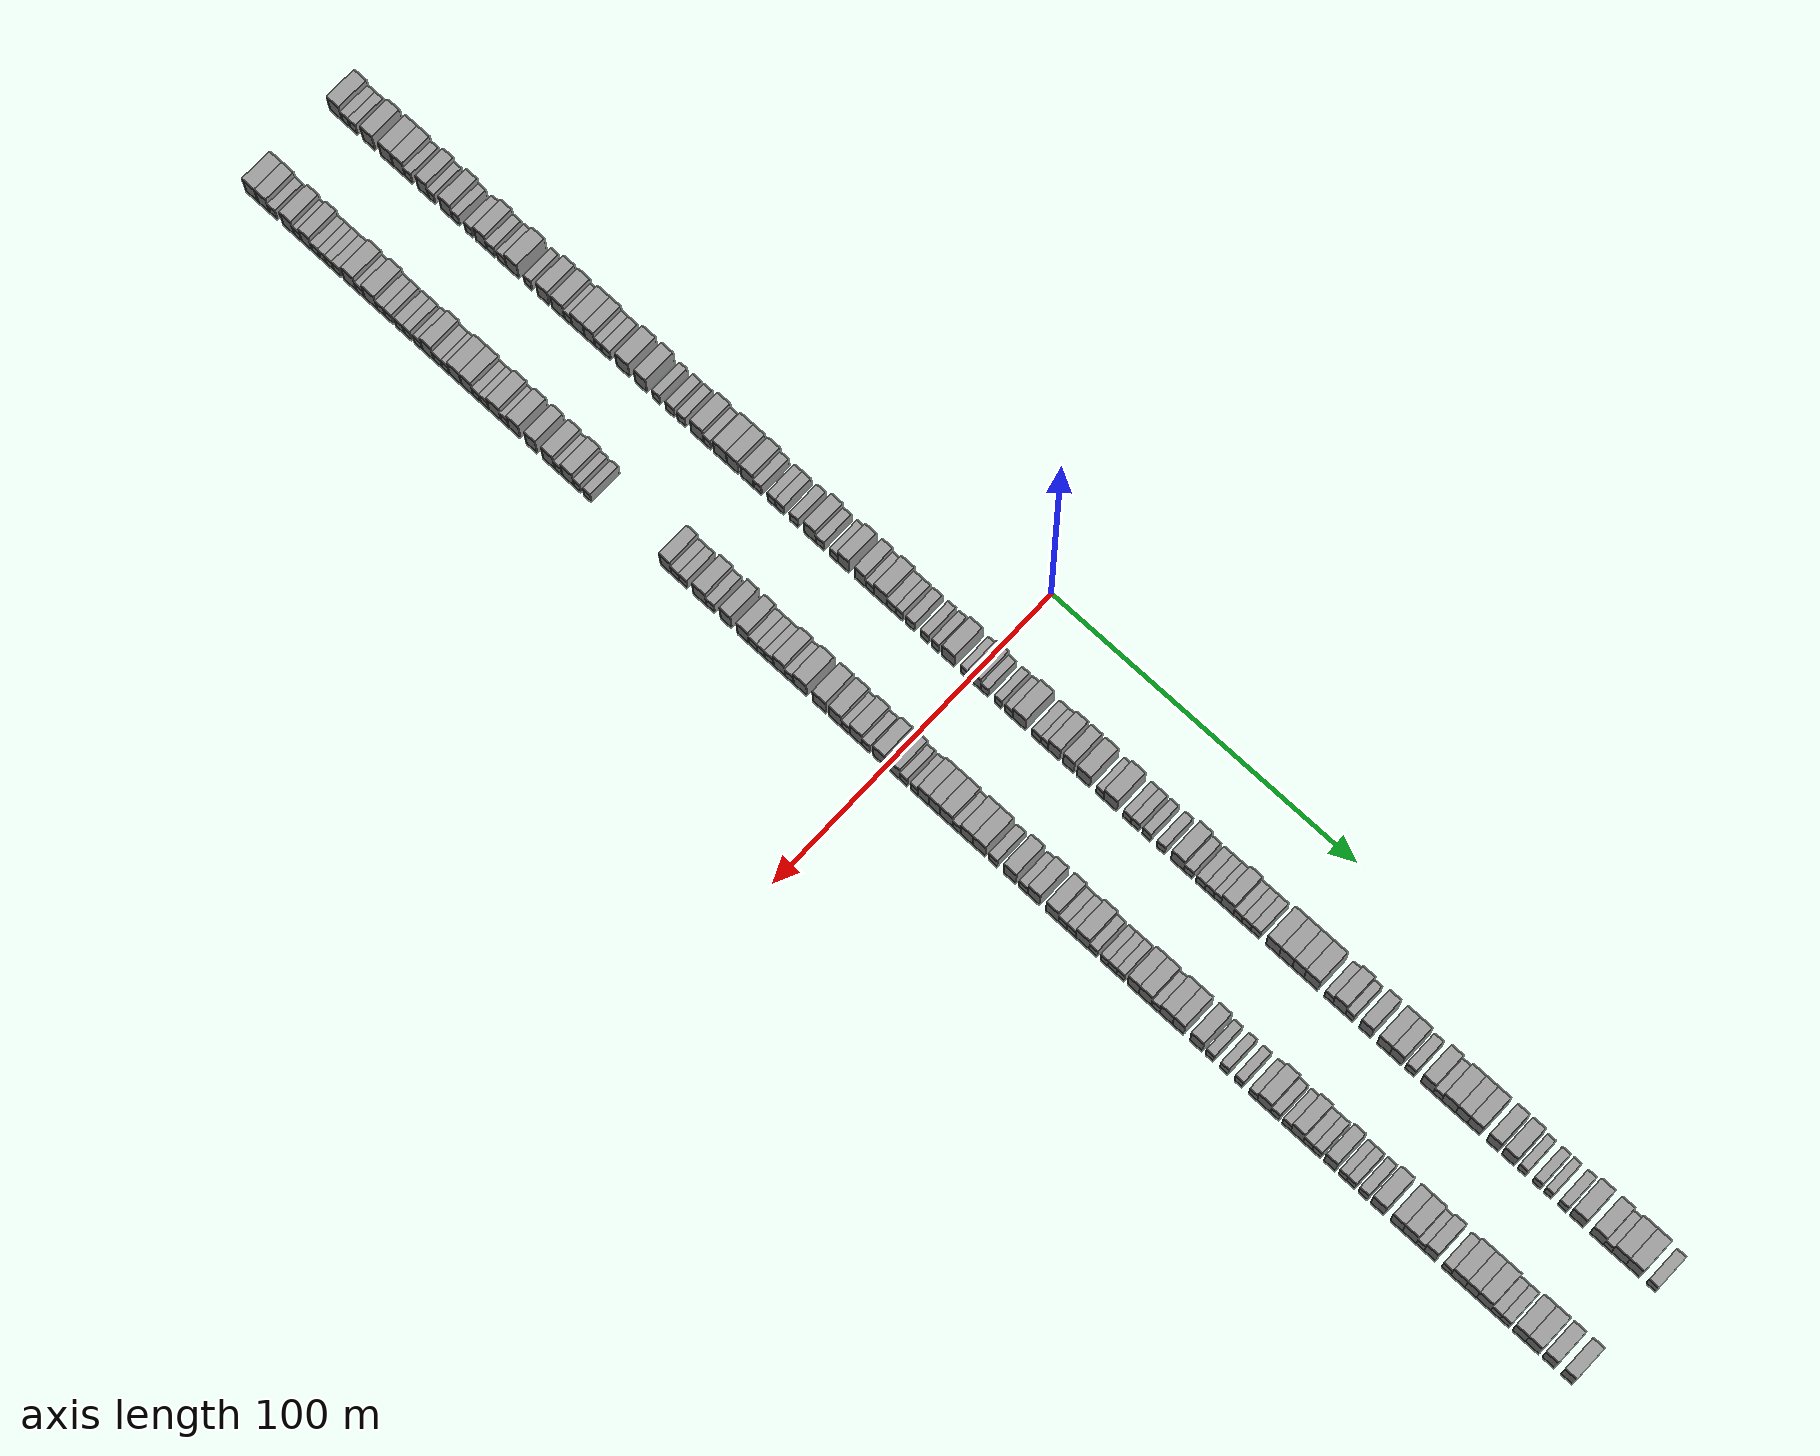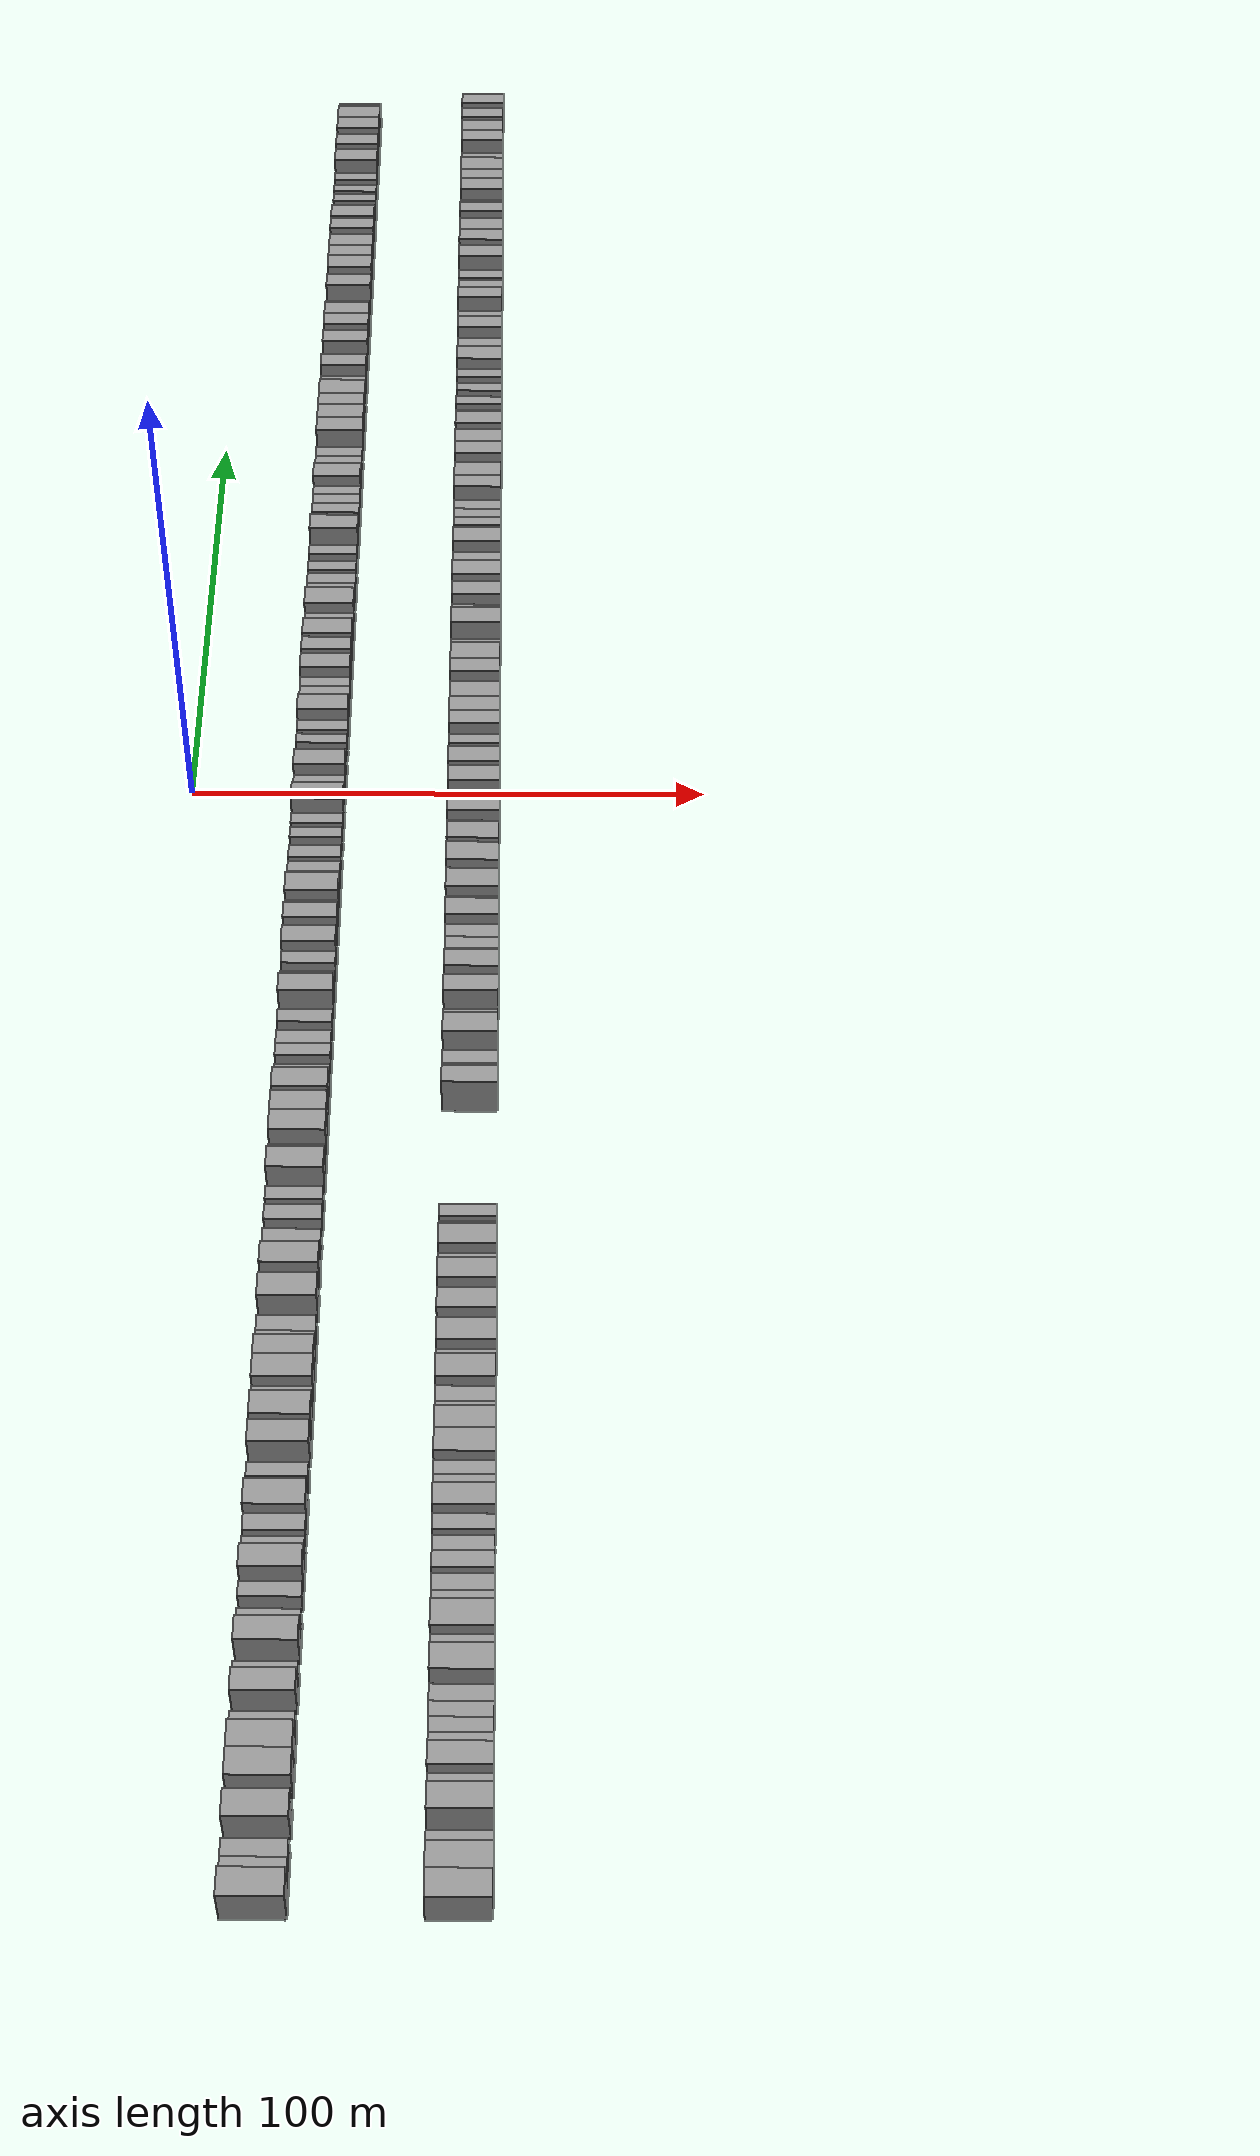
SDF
<sdf version="1.6">
 <world name="default">
  <scene>
   <sky><clouds><speed>12</speed></clouds></sky>
   <ambient>0.4 0.4 0.4 1</ambient>
   <background>0.7 0.7 0.7 1</background>
   <shadows>1</shadows>
  </scene>
  <gravity>0 0 -9.8066</gravity>
  <magnetic_field>6e-06 2.3e-05 -4.2e-05</magnetic_field>
  <physics default="0" name="default_physics" type="ode">
   <ode>
    <solver>
     <type>quick</type>
     <iters>10</iters>
     <sor>1.0</sor>
     <use_dynamic_moi_rescaling>0</use_dynamic_moi_rescaling>
    </solver>
    <constraints>
     <cfm>0</cfm>
     <erp>0.2</erp>
     <contact_max_correcting_vel>100</contact_max_correcting_vel>
     <contact_surface_layer>0.001</contact_surface_layer>
    </constraints>
   </ode>
   <max_step_size>0.004</max_step_size>
   <real_time_factor>1</real_time_factor>
   <real_time_update_rate>250</real_time_update_rate>
  </physics>
  <light name="sun" type="directional">
   <pose>0 0 10 0 0 0</pose>
   <diffuse>0.8 0.8 0.8 1</diffuse>
   <specular>0.2 0.2 0.2 1</specular>
   <attenuation>
    <range>1000</range>
    <constant>0.9</constant>
    <linear>0.01</linear>
    <quadratic>0.001</quadratic>
   </attenuation>
   <direction>-0.5 0.1 -0.9</direction>
  </light>
  <model name="building_1">
   <static>1</static>
   <pose>25.0000 -217.8463 0 0.000000 0.000000 0.000000</pose>
   <link name="link">
    <pose>0 0 4.50 0 0 0</pose>
    <collision name="collision"><geometry><box><size>10.0000 4.3074 9.0000</size></box></geometry></collision>
    <visual name="visual">
     <cast_shadows>0</cast_shadows>
     <geometry><box><size>10.0000 4.3074 9.0000</size></box></geometry>
     <material>
      <script>
       <uri>model://grey_wall/materials/scripts</uri>
       <uri>model://grey_wall/materials/textures</uri>
       <name>vrc/grey_wall</name>
      </script>
     </material>
    </visual>
   </link>
  </model>
  <model name="building_2">
   <static>1</static>
   <pose>25.0000 -214.3523 0 0.000000 0.000000 0.000000</pose>
   <link name="link">
    <pose>0 0 3.00 0 0 0</pose>
    <collision name="collision"><geometry><box><size>10.0000 2.6805 6.0000</size></box></geometry></collision>
    <visual name="visual">
     <cast_shadows>0</cast_shadows>
     <geometry><box><size>10.0000 2.6805 6.0000</size></box></geometry>
     <material>
      <script>
       <uri>model://grey_wall/materials/scripts</uri>
       <uri>model://grey_wall/materials/textures</uri>
       <name>vrc/grey_wall</name>
      </script>
     </material>
    </visual>
   </link>
  </model>
  <model name="building_3">
   <static>1</static>
   <pose>25.0000 -211.6491 0 0.000000 0.000000 0.000000</pose>
   <link name="link">
    <pose>0 0 3.00 0 0 0</pose>
    <collision name="collision"><geometry><box><size>10.0000 2.7260 6.0000</size></box></geometry></collision>
    <visual name="visual">
     <cast_shadows>0</cast_shadows>
     <geometry><box><size>10.0000 2.7260 6.0000</size></box></geometry>
     <material>
      <script>
       <uri>model://grey_wall/materials/scripts</uri>
       <uri>model://grey_wall/materials/textures</uri>
       <name>vrc/grey_wall</name>
      </script>
     </material>
    </visual>
   </link>
  </model>
  <model name="building_4">
   <static>1</static>
   <pose>25.0000 -206.1465 0 0.000000 0.000000 0.000000</pose>
   <link name="link">
    <pose>0 0 4.50 0 0 0</pose>
    <collision name="collision"><geometry><box><size>10.0000 4.2792 9.0000</size></box></geometry></collision>
    <visual name="visual">
     <cast_shadows>0</cast_shadows>
     <geometry><box><size>10.0000 4.2792 9.0000</size></box></geometry>
     <material>
      <script>
       <uri>model://grey_wall/materials/scripts</uri>
       <uri>model://grey_wall/materials/textures</uri>
       <name>vrc/grey_wall</name>
      </script>
     </material>
    </visual>
   </link>
  </model>
  <model name="building_5">
   <static>1</static>
   <pose>25.0000 -199.8530 0 0.000000 0.000000 0.000000</pose>
   <link name="link">
    <pose>0 0 4.50 0 0 0</pose>
    <collision name="collision"><geometry><box><size>10.0000 4.3078 9.0000</size></box></geometry></collision>
    <visual name="visual">
     <cast_shadows>0</cast_shadows>
     <geometry><box><size>10.0000 4.3078 9.0000</size></box></geometry>
     <material>
      <script>
       <uri>model://grey_wall/materials/scripts</uri>
       <uri>model://grey_wall/materials/textures</uri>
       <name>vrc/grey_wall</name>
      </script>
     </material>
    </visual>
   </link>
  </model>
  <model name="building_6">
   <static>1</static>
   <pose>25.0000 -195.5964 0 0.000000 0.000000 0.000000</pose>
   <link name="link">
    <pose>0 0 4.50 0 0 0</pose>
    <collision name="collision"><geometry><box><size>10.0000 4.2055 9.0000</size></box></geometry></collision>
    <visual name="visual">
     <cast_shadows>0</cast_shadows>
     <geometry><box><size>10.0000 4.2055 9.0000</size></box></geometry>
     <material>
      <script>
       <uri>model://grey_wall/materials/scripts</uri>
       <uri>model://grey_wall/materials/textures</uri>
       <name>vrc/grey_wall</name>
      </script>
     </material>
    </visual>
   </link>
  </model>
  <model name="building_7">
   <static>1</static>
   <pose>25.0000 -192.1730 0 0.000000 0.000000 0.000000</pose>
   <link name="link">
    <pose>0 0 3.00 0 0 0</pose>
    <collision name="collision"><geometry><box><size>10.0000 2.6413 6.0000</size></box></geometry></collision>
    <visual name="visual">
     <cast_shadows>0</cast_shadows>
     <geometry><box><size>10.0000 2.6413 6.0000</size></box></geometry>
     <material>
      <script>
       <uri>model://grey_wall/materials/scripts</uri>
       <uri>model://grey_wall/materials/textures</uri>
       <name>vrc/grey_wall</name>
      </script>
     </material>
    </visual>
   </link>
  </model>
  <model name="building_8">
   <static>1</static>
   <pose>25.0000 -187.0257 0 0.000000 0.000000 0.000000</pose>
   <link name="link">
    <pose>0 0 4.50 0 0 0</pose>
    <collision name="collision"><geometry><box><size>10.0000 3.6533 9.0000</size></box></geometry></collision>
    <visual name="visual">
     <cast_shadows>0</cast_shadows>
     <geometry><box><size>10.0000 3.6533 9.0000</size></box></geometry>
     <material>
      <script>
       <uri>model://grey_wall/materials/scripts</uri>
       <uri>model://grey_wall/materials/textures</uri>
       <name>vrc/grey_wall</name>
      </script>
     </material>
    </visual>
   </link>
  </model>
  <model name="building_9">
   <static>1</static>
   <pose>25.0000 -183.9845 0 0.000000 0.000000 0.000000</pose>
   <link name="link">
    <pose>0 0 3.00 0 0 0</pose>
    <collision name="collision"><geometry><box><size>10.0000 2.4291 6.0000</size></box></geometry></collision>
    <visual name="visual">
     <cast_shadows>0</cast_shadows>
     <geometry><box><size>10.0000 2.4291 6.0000</size></box></geometry>
     <material>
      <script>
       <uri>model://grey_wall/materials/scripts</uri>
       <uri>model://grey_wall/materials/textures</uri>
       <name>vrc/grey_wall</name>
      </script>
     </material>
    </visual>
   </link>
  </model>
  <model name="building_10">
   <static>1</static>
   <pose>25.0000 -178.7995 0 0.000000 0.000000 0.000000</pose>
   <link name="link">
    <pose>0 0 4.50 0 0 0</pose>
    <collision name="collision"><geometry><box><size>10.0000 3.9409 9.0000</size></box></geometry></collision>
    <visual name="visual">
     <cast_shadows>0</cast_shadows>
     <geometry><box><size>10.0000 3.9409 9.0000</size></box></geometry>
     <material>
      <script>
       <uri>model://grey_wall/materials/scripts</uri>
       <uri>model://grey_wall/materials/textures</uri>
       <name>vrc/grey_wall</name>
      </script>
     </material>
    </visual>
   </link>
  </model>
  <model name="building_11">
   <static>1</static>
   <pose>25.0000 -175.5220 0 0.000000 0.000000 0.000000</pose>
   <link name="link">
    <pose>0 0 3.00 0 0 0</pose>
    <collision name="collision"><geometry><box><size>10.0000 2.6142 6.0000</size></box></geometry></collision>
    <visual name="visual">
     <cast_shadows>0</cast_shadows>
     <geometry><box><size>10.0000 2.6142 6.0000</size></box></geometry>
     <material>
      <script>
       <uri>model://grey_wall/materials/scripts</uri>
       <uri>model://grey_wall/materials/textures</uri>
       <name>vrc/grey_wall</name>
      </script>
     </material>
    </visual>
   </link>
  </model>
  <model name="building_12">
   <static>1</static>
   <pose>25.0000 -170.9310 0 0.000000 0.000000 0.000000</pose>
   <link name="link">
    <pose>0 0 3.00 0 0 0</pose>
    <collision name="collision"><geometry><box><size>10.0000 2.5679 6.0000</size></box></geometry></collision>
    <visual name="visual">
     <cast_shadows>0</cast_shadows>
     <geometry><box><size>10.0000 2.5679 6.0000</size></box></geometry>
     <material>
      <script>
       <uri>model://grey_wall/materials/scripts</uri>
       <uri>model://grey_wall/materials/textures</uri>
       <name>vrc/grey_wall</name>
      </script>
     </material>
    </visual>
   </link>
  </model>
  <model name="building_13">
   <static>1</static>
   <pose>25.0000 -166.7279 0 0.000000 0.000000 0.000000</pose>
   <link name="link">
    <pose>0 0 4.50 0 0 0</pose>
    <collision name="collision"><geometry><box><size>10.0000 3.8383 9.0000</size></box></geometry></collision>
    <visual name="visual">
     <cast_shadows>0</cast_shadows>
     <geometry><box><size>10.0000 3.8383 9.0000</size></box></geometry>
     <material>
      <script>
       <uri>model://grey_wall/materials/scripts</uri>
       <uri>model://grey_wall/materials/textures</uri>
       <name>vrc/grey_wall</name>
      </script>
     </material>
    </visual>
   </link>
  </model>
  <model name="building_14">
   <static>1</static>
   <pose>25.0000 -163.3704 0 0.000000 0.000000 0.000000</pose>
   <link name="link">
    <pose>0 0 3.00 0 0 0</pose>
    <collision name="collision"><geometry><box><size>10.0000 2.8766 6.0000</size></box></geometry></collision>
    <visual name="visual">
     <cast_shadows>0</cast_shadows>
     <geometry><box><size>10.0000 2.8766 6.0000</size></box></geometry>
     <material>
      <script>
       <uri>model://grey_wall/materials/scripts</uri>
       <uri>model://grey_wall/materials/textures</uri>
       <name>vrc/grey_wall</name>
      </script>
     </material>
    </visual>
   </link>
  </model>
  <model name="building_15">
   <static>1</static>
   <pose>25.0000 -159.4511 0 0.000000 0.000000 0.000000</pose>
   <link name="link">
    <pose>0 0 3.00 0 0 0</pose>
    <collision name="collision"><geometry><box><size>10.0000 2.9620 6.0000</size></box></geometry></collision>
    <visual name="visual">
     <cast_shadows>0</cast_shadows>
     <geometry><box><size>10.0000 2.9620 6.0000</size></box></geometry>
     <material>
      <script>
       <uri>model://grey_wall/materials/scripts</uri>
       <uri>model://grey_wall/materials/textures</uri>
       <name>vrc/grey_wall</name>
      </script>
     </material>
    </visual>
   </link>
  </model>
  <model name="building_16">
   <static>1</static>
   <pose>25.0000 -155.7571 0 0.000000 0.000000 0.000000</pose>
   <link name="link">
    <pose>0 0 4.50 0 0 0</pose>
    <collision name="collision"><geometry><box><size>10.0000 4.4260 9.0000</size></box></geometry></collision>
    <visual name="visual">
     <cast_shadows>0</cast_shadows>
     <geometry><box><size>10.0000 4.4260 9.0000</size></box></geometry>
     <material>
      <script>
       <uri>model://grey_wall/materials/scripts</uri>
       <uri>model://grey_wall/materials/textures</uri>
       <name>vrc/grey_wall</name>
      </script>
     </material>
    </visual>
   </link>
  </model>
  <model name="building_17">
   <static>1</static>
   <pose>25.0000 -150.2537 0 0.000000 0.000000 0.000000</pose>
   <link name="link">
    <pose>0 0 3.00 0 0 0</pose>
    <collision name="collision"><geometry><box><size>10.0000 2.5807 6.0000</size></box></geometry></collision>
    <visual name="visual">
     <cast_shadows>0</cast_shadows>
     <geometry><box><size>10.0000 2.5807 6.0000</size></box></geometry>
     <material>
      <script>
       <uri>model://grey_wall/materials/scripts</uri>
       <uri>model://grey_wall/materials/textures</uri>
       <name>vrc/grey_wall</name>
      </script>
     </material>
    </visual>
   </link>
  </model>
  <model name="building_18">
   <static>1</static>
   <pose>25.0000 -144.9676 0 0.000000 0.000000 0.000000</pose>
   <link name="link">
    <pose>0 0 4.50 0 0 0</pose>
    <collision name="collision"><geometry><box><size>10.0000 3.9914 9.0000</size></box></geometry></collision>
    <visual name="visual">
     <cast_shadows>0</cast_shadows>
     <geometry><box><size>10.0000 3.9914 9.0000</size></box></geometry>
     <material>
      <script>
       <uri>model://grey_wall/materials/scripts</uri>
       <uri>model://grey_wall/materials/textures</uri>
       <name>vrc/grey_wall</name>
      </script>
     </material>
    </visual>
   </link>
  </model>
  <model name="building_19">
   <static>1</static>
   <pose>25.0000 -139.8458 0 0.000000 0.000000 0.000000</pose>
   <link name="link">
    <pose>0 0 4.50 0 0 0</pose>
    <collision name="collision"><geometry><box><size>10.0000 4.2523 9.0000</size></box></geometry></collision>
    <visual name="visual">
     <cast_shadows>0</cast_shadows>
     <geometry><box><size>10.0000 4.2523 9.0000</size></box></geometry>
     <material>
      <script>
       <uri>model://grey_wall/materials/scripts</uri>
       <uri>model://grey_wall/materials/textures</uri>
       <name>vrc/grey_wall</name>
      </script>
     </material>
    </visual>
   </link>
  </model>
  <model name="building_20">
   <static>1</static>
   <pose>25.0000 -136.4243 0 0.000000 0.000000 0.000000</pose>
   <link name="link">
    <pose>0 0 3.00 0 0 0</pose>
    <collision name="collision"><geometry><box><size>10.0000 2.5906 6.0000</size></box></geometry></collision>
    <visual name="visual">
     <cast_shadows>0</cast_shadows>
     <geometry><box><size>10.0000 2.5906 6.0000</size></box></geometry>
     <material>
      <script>
       <uri>model://grey_wall/materials/scripts</uri>
       <uri>model://grey_wall/materials/textures</uri>
       <name>vrc/grey_wall</name>
      </script>
     </material>
    </visual>
   </link>
  </model>
  <model name="building_21">
   <static>1</static>
   <pose>25.0000 -132.9576 0 0.000000 0.000000 0.000000</pose>
   <link name="link">
    <pose>0 0 4.50 0 0 0</pose>
    <collision name="collision"><geometry><box><size>10.0000 4.3429 9.0000</size></box></geometry></collision>
    <visual name="visual">
     <cast_shadows>0</cast_shadows>
     <geometry><box><size>10.0000 4.3429 9.0000</size></box></geometry>
     <material>
      <script>
       <uri>model://grey_wall/materials/scripts</uri>
       <uri>model://grey_wall/materials/textures</uri>
       <name>vrc/grey_wall</name>
      </script>
     </material>
    </visual>
   </link>
  </model>
  <model name="building_22">
   <static>1</static>
   <pose>25.0000 -128.9731 0 0.000000 0.000000 0.000000</pose>
   <link name="link">
    <pose>0 0 4.50 0 0 0</pose>
    <collision name="collision"><geometry><box><size>10.0000 3.6260 9.0000</size></box></geometry></collision>
    <visual name="visual">
     <cast_shadows>0</cast_shadows>
     <geometry><box><size>10.0000 3.6260 9.0000</size></box></geometry>
     <material>
      <script>
       <uri>model://grey_wall/materials/scripts</uri>
       <uri>model://grey_wall/materials/textures</uri>
       <name>vrc/grey_wall</name>
      </script>
     </material>
    </visual>
   </link>
  </model>
  <model name="building_23">
   <static>1</static>
   <pose>25.0000 -125.9395 0 0.000000 0.000000 0.000000</pose>
   <link name="link">
    <pose>0 0 3.00 0 0 0</pose>
    <collision name="collision"><geometry><box><size>10.0000 2.4413 6.0000</size></box></geometry></collision>
    <visual name="visual">
     <cast_shadows>0</cast_shadows>
     <geometry><box><size>10.0000 2.4413 6.0000</size></box></geometry>
     <material>
      <script>
       <uri>model://grey_wall/materials/scripts</uri>
       <uri>model://grey_wall/materials/textures</uri>
       <name>vrc/grey_wall</name>
      </script>
     </material>
    </visual>
   </link>
  </model>
  <model name="building_24">
   <static>1</static>
   <pose>25.0000 -123.2206 0 0.000000 0.000000 0.000000</pose>
   <link name="link">
    <pose>0 0 3.00 0 0 0</pose>
    <collision name="collision"><geometry><box><size>10.0000 2.9964 6.0000</size></box></geometry></collision>
    <visual name="visual">
     <cast_shadows>0</cast_shadows>
     <geometry><box><size>10.0000 2.9964 6.0000</size></box></geometry>
     <material>
      <script>
       <uri>model://grey_wall/materials/scripts</uri>
       <uri>model://grey_wall/materials/textures</uri>
       <name>vrc/grey_wall</name>
      </script>
     </material>
    </visual>
   </link>
  </model>
  <model name="building_25">
   <static>1</static>
   <pose>25.0000 -117.4849 0 0.000000 0.000000 0.000000</pose>
   <link name="link">
    <pose>0 0 4.50 0 0 0</pose>
    <collision name="collision"><geometry><box><size>10.0000 4.4751 9.0000</size></box></geometry></collision>
    <visual name="visual">
     <cast_shadows>0</cast_shadows>
     <geometry><box><size>10.0000 4.4751 9.0000</size></box></geometry>
     <material>
      <script>
       <uri>model://grey_wall/materials/scripts</uri>
       <uri>model://grey_wall/materials/textures</uri>
       <name>vrc/grey_wall</name>
      </script>
     </material>
    </visual>
   </link>
  </model>
  <model name="building_26">
   <static>1</static>
   <pose>25.0000 -111.2404 0 0.000000 0.000000 0.000000</pose>
   <link name="link">
    <pose>0 0 4.50 0 0 0</pose>
    <collision name="collision"><geometry><box><size>10.0000 4.0138 9.0000</size></box></geometry></collision>
    <visual name="visual">
     <cast_shadows>0</cast_shadows>
     <geometry><box><size>10.0000 4.0138 9.0000</size></box></geometry>
     <material>
      <script>
       <uri>model://grey_wall/materials/scripts</uri>
       <uri>model://grey_wall/materials/textures</uri>
       <name>vrc/grey_wall</name>
      </script>
     </material>
    </visual>
   </link>
  </model>
  <model name="building_27">
   <static>1</static>
   <pose>25.0000 -105.9626 0 0.000000 0.000000 0.000000</pose>
   <link name="link">
    <pose>0 0 3.00 0 0 0</pose>
    <collision name="collision"><geometry><box><size>10.0000 2.5419 6.0000</size></box></geometry></collision>
    <visual name="visual">
     <cast_shadows>0</cast_shadows>
     <geometry><box><size>10.0000 2.5419 6.0000</size></box></geometry>
     <material>
      <script>
       <uri>model://grey_wall/materials/scripts</uri>
       <uri>model://grey_wall/materials/textures</uri>
       <name>vrc/grey_wall</name>
      </script>
     </material>
    </visual>
   </link>
  </model>
  <model name="building_28">
   <static>1</static>
   <pose>25.0000 -101.2293 0 0.000000 0.000000 0.000000</pose>
   <link name="link">
    <pose>0 0 3.00 0 0 0</pose>
    <collision name="collision"><geometry><box><size>10.0000 2.9246 6.0000</size></box></geometry></collision>
    <visual name="visual">
     <cast_shadows>0</cast_shadows>
     <geometry><box><size>10.0000 2.9246 6.0000</size></box></geometry>
     <material>
      <script>
       <uri>model://grey_wall/materials/scripts</uri>
       <uri>model://grey_wall/materials/textures</uri>
       <name>vrc/grey_wall</name>
      </script>
     </material>
    </visual>
   </link>
  </model>
  <model name="building_29">
   <static>1</static>
   <pose>25.0000 -97.4095 0 0.000000 0.000000 0.000000</pose>
   <link name="link">
    <pose>0 0 3.00 0 0 0</pose>
    <collision name="collision"><geometry><box><size>10.0000 2.7150 6.0000</size></box></geometry></collision>
    <visual name="visual">
     <cast_shadows>0</cast_shadows>
     <geometry><box><size>10.0000 2.7150 6.0000</size></box></geometry>
     <material>
      <script>
       <uri>model://grey_wall/materials/scripts</uri>
       <uri>model://grey_wall/materials/textures</uri>
       <name>vrc/grey_wall</name>
      </script>
     </material>
    </visual>
   </link>
  </model>
  <model name="building_30">
   <static>1</static>
   <pose>25.0000 -91.9253 0 0.000000 0.000000 0.000000</pose>
   <link name="link">
    <pose>0 0 4.50 0 0 0</pose>
    <collision name="collision"><geometry><box><size>10.0000 4.2534 9.0000</size></box></geometry></collision>
    <visual name="visual">
     <cast_shadows>0</cast_shadows>
     <geometry><box><size>10.0000 4.2534 9.0000</size></box></geometry>
     <material>
      <script>
       <uri>model://grey_wall/materials/scripts</uri>
       <uri>model://grey_wall/materials/textures</uri>
       <name>vrc/grey_wall</name>
      </script>
     </material>
    </visual>
   </link>
  </model>
  <model name="building_31">
   <static>1</static>
   <pose>25.0000 -88.5392 0 0.000000 0.000000 0.000000</pose>
   <link name="link">
    <pose>0 0 3.00 0 0 0</pose>
    <collision name="collision"><geometry><box><size>10.0000 2.5188 6.0000</size></box></geometry></collision>
    <visual name="visual">
     <cast_shadows>0</cast_shadows>
     <geometry><box><size>10.0000 2.5188 6.0000</size></box></geometry>
     <material>
      <script>
       <uri>model://grey_wall/materials/scripts</uri>
       <uri>model://grey_wall/materials/textures</uri>
       <name>vrc/grey_wall</name>
      </script>
     </material>
    </visual>
   </link>
  </model>
  <model name="building_32">
   <static>1</static>
   <pose>25.0000 -84.0698 0 0.000000 0.000000 0.000000</pose>
   <link name="link">
    <pose>0 0 4.50 0 0 0</pose>
    <collision name="collision"><geometry><box><size>10.0000 4.4201 9.0000</size></box></geometry></collision>
    <visual name="visual">
     <cast_shadows>0</cast_shadows>
     <geometry><box><size>10.0000 4.4201 9.0000</size></box></geometry>
     <material>
      <script>
       <uri>model://grey_wall/materials/scripts</uri>
       <uri>model://grey_wall/materials/textures</uri>
       <name>vrc/grey_wall</name>
      </script>
     </material>
    </visual>
   </link>
  </model>
  <model name="building_33">
   <static>1</static>
   <pose>25.0000 -79.8985 0 0.000000 0.000000 0.000000</pose>
   <link name="link">
    <pose>0 0 4.50 0 0 0</pose>
    <collision name="collision"><geometry><box><size>10.0000 3.9224 9.0000</size></box></geometry></collision>
    <visual name="visual">
     <cast_shadows>0</cast_shadows>
     <geometry><box><size>10.0000 3.9224 9.0000</size></box></geometry>
     <material>
      <script>
       <uri>model://grey_wall/materials/scripts</uri>
       <uri>model://grey_wall/materials/textures</uri>
       <name>vrc/grey_wall</name>
      </script>
     </material>
    </visual>
   </link>
  </model>
  <model name="building_34">
   <static>1</static>
   <pose>25.0000 -74.8766 0 0.000000 0.000000 0.000000</pose>
   <link name="link">
    <pose>0 0 4.50 0 0 0</pose>
    <collision name="collision"><geometry><box><size>10.0000 4.1214 9.0000</size></box></geometry></collision>
    <visual name="visual">
     <cast_shadows>0</cast_shadows>
     <geometry><box><size>10.0000 4.1214 9.0000</size></box></geometry>
     <material>
      <script>
       <uri>model://grey_wall/materials/scripts</uri>
       <uri>model://grey_wall/materials/textures</uri>
       <name>vrc/grey_wall</name>
      </script>
     </material>
    </visual>
   </link>
  </model>
  <model name="building_35">
   <static>1</static>
   <pose>25.0000 -71.4069 0 0.000000 0.000000 0.000000</pose>
   <link name="link">
    <pose>0 0 3.00 0 0 0</pose>
    <collision name="collision"><geometry><box><size>10.0000 2.8181 6.0000</size></box></geometry></collision>
    <visual name="visual">
     <cast_shadows>0</cast_shadows>
     <geometry><box><size>10.0000 2.8181 6.0000</size></box></geometry>
     <material>
      <script>
       <uri>model://grey_wall/materials/scripts</uri>
       <uri>model://grey_wall/materials/textures</uri>
       <name>vrc/grey_wall</name>
      </script>
     </material>
    </visual>
   </link>
  </model>
  <model name="building_36">
   <static>1</static>
   <pose>25.0000 -66.6656 0 0.000000 0.000000 0.000000</pose>
   <link name="link">
    <pose>0 0 3.00 0 0 0</pose>
    <collision name="collision"><geometry><box><size>10.0000 2.6644 6.0000</size></box></geometry></collision>
    <visual name="visual">
     <cast_shadows>0</cast_shadows>
     <geometry><box><size>10.0000 2.6644 6.0000</size></box></geometry>
     <material>
      <script>
       <uri>model://grey_wall/materials/scripts</uri>
       <uri>model://grey_wall/materials/textures</uri>
       <name>vrc/grey_wall</name>
      </script>
     </material>
    </visual>
   </link>
  </model>
  <model name="building_37">
   <static>1</static>
   <pose>25.0000 -63.8948 0 0.000000 0.000000 0.000000</pose>
   <link name="link">
    <pose>0 0 3.00 0 0 0</pose>
    <collision name="collision"><geometry><box><size>10.0000 2.8771 6.0000</size></box></geometry></collision>
    <visual name="visual">
     <cast_shadows>0</cast_shadows>
     <geometry><box><size>10.0000 2.8771 6.0000</size></box></geometry>
     <material>
      <script>
       <uri>model://grey_wall/materials/scripts</uri>
       <uri>model://grey_wall/materials/textures</uri>
       <name>vrc/grey_wall</name>
      </script>
     </material>
    </visual>
   </link>
  </model>
  <model name="building_38">
   <static>1</static>
   <pose>25.0000 -58.9998 0 0.000000 0.000000 0.000000</pose>
   <link name="link">
    <pose>0 0 3.00 0 0 0</pose>
    <collision name="collision"><geometry><box><size>10.0000 2.9128 6.0000</size></box></geometry></collision>
    <visual name="visual">
     <cast_shadows>0</cast_shadows>
     <geometry><box><size>10.0000 2.9128 6.0000</size></box></geometry>
     <material>
      <script>
       <uri>model://grey_wall/materials/scripts</uri>
       <uri>model://grey_wall/materials/textures</uri>
       <name>vrc/grey_wall</name>
      </script>
     </material>
    </visual>
   </link>
  </model>
  <model name="building_39">
   <static>1</static>
   <pose>25.0000 -53.5997 0 0.000000 0.000000 0.000000</pose>
   <link name="link">
    <pose>0 0 4.50 0 0 0</pose>
    <collision name="collision"><geometry><box><size>10.0000 3.8875 9.0000</size></box></geometry></collision>
    <visual name="visual">
     <cast_shadows>0</cast_shadows>
     <geometry><box><size>10.0000 3.8875 9.0000</size></box></geometry>
     <material>
      <script>
       <uri>model://grey_wall/materials/scripts</uri>
       <uri>model://grey_wall/materials/textures</uri>
       <name>vrc/grey_wall</name>
      </script>
     </material>
    </visual>
   </link>
  </model>
  <model name="building_40">
   <static>1</static>
   <pose>25.0000 -50.2685 0 0.000000 0.000000 0.000000</pose>
   <link name="link">
    <pose>0 0 3.00 0 0 0</pose>
    <collision name="collision"><geometry><box><size>10.0000 2.7749 6.0000</size></box></geometry></collision>
    <visual name="visual">
     <cast_shadows>0</cast_shadows>
     <geometry><box><size>10.0000 2.7749 6.0000</size></box></geometry>
     <material>
      <script>
       <uri>model://grey_wall/materials/scripts</uri>
       <uri>model://grey_wall/materials/textures</uri>
       <name>vrc/grey_wall</name>
      </script>
     </material>
    </visual>
   </link>
  </model>
  <model name="building_41">
   <static>1</static>
   <pose>25.0000 -45.5206 0 0.000000 0.000000 0.000000</pose>
   <link name="link">
    <pose>0 0 3.00 0 0 0</pose>
    <collision name="collision"><geometry><box><size>10.0000 2.7209 6.0000</size></box></geometry></collision>
    <visual name="visual">
     <cast_shadows>0</cast_shadows>
     <geometry><box><size>10.0000 2.7209 6.0000</size></box></geometry>
     <material>
      <script>
       <uri>model://grey_wall/materials/scripts</uri>
       <uri>model://grey_wall/materials/textures</uri>
       <name>vrc/grey_wall</name>
      </script>
     </material>
    </visual>
   </link>
  </model>
  <model name="building_42">
   <static>1</static>
   <pose>25.0000 -42.3078 0 0.000000 0.000000 0.000000</pose>
   <link name="link">
    <pose>0 0 4.50 0 0 0</pose>
    <collision name="collision"><geometry><box><size>10.0000 3.7046 9.0000</size></box></geometry></collision>
    <visual name="visual">
     <cast_shadows>0</cast_shadows>
     <geometry><box><size>10.0000 3.7046 9.0000</size></box></geometry>
     <material>
      <script>
       <uri>model://grey_wall/materials/scripts</uri>
       <uri>model://grey_wall/materials/textures</uri>
       <name>vrc/grey_wall</name>
      </script>
     </material>
    </visual>
   </link>
  </model>
  <model name="building_43">
   <static>1</static>
   <pose>25.0000 -36.6553 0 0.000000 0.000000 0.000000</pose>
   <link name="link">
    <pose>0 0 4.50 0 0 0</pose>
    <collision name="collision"><geometry><box><size>10.0000 3.6004 9.0000</size></box></geometry></collision>
    <visual name="visual">
     <cast_shadows>0</cast_shadows>
     <geometry><box><size>10.0000 3.6004 9.0000</size></box></geometry>
     <material>
      <script>
       <uri>model://grey_wall/materials/scripts</uri>
       <uri>model://grey_wall/materials/textures</uri>
       <name>vrc/grey_wall</name>
      </script>
     </material>
    </visual>
   </link>
  </model>
  <model name="building_44">
   <static>1</static>
   <pose>25.0000 -33.4309 0 0.000000 0.000000 0.000000</pose>
   <link name="link">
    <pose>0 0 3.00 0 0 0</pose>
    <collision name="collision"><geometry><box><size>10.0000 2.8486 6.0000</size></box></geometry></collision>
    <visual name="visual">
     <cast_shadows>0</cast_shadows>
     <geometry><box><size>10.0000 2.8486 6.0000</size></box></geometry>
     <material>
      <script>
       <uri>model://grey_wall/materials/scripts</uri>
       <uri>model://grey_wall/materials/textures</uri>
       <name>vrc/grey_wall</name>
      </script>
     </material>
    </visual>
   </link>
  </model>
  <model name="building_45">
   <static>1</static>
   <pose>25.0000 -29.8701 0 0.000000 0.000000 0.000000</pose>
   <link name="link">
    <pose>0 0 4.50 0 0 0</pose>
    <collision name="collision"><geometry><box><size>10.0000 4.2731 9.0000</size></box></geometry></collision>
    <visual name="visual">
     <cast_shadows>0</cast_shadows>
     <geometry><box><size>10.0000 4.2731 9.0000</size></box></geometry>
     <material>
      <script>
       <uri>model://grey_wall/materials/scripts</uri>
       <uri>model://grey_wall/materials/textures</uri>
       <name>vrc/grey_wall</name>
      </script>
     </material>
    </visual>
   </link>
  </model>
  <model name="building_46">
   <static>1</static>
   <pose>25.0000 -26.2513 0 0.000000 0.000000 0.000000</pose>
   <link name="link">
    <pose>0 0 3.00 0 0 0</pose>
    <collision name="collision"><geometry><box><size>10.0000 2.9645 6.0000</size></box></geometry></collision>
    <visual name="visual">
     <cast_shadows>0</cast_shadows>
     <geometry><box><size>10.0000 2.9645 6.0000</size></box></geometry>
     <material>
      <script>
       <uri>model://grey_wall/materials/scripts</uri>
       <uri>model://grey_wall/materials/textures</uri>
       <name>vrc/grey_wall</name>
      </script>
     </material>
    </visual>
   </link>
  </model>
  <model name="building_47">
   <static>1</static>
   <pose>25.0000 -23.5594 0 0.000000 0.000000 0.000000</pose>
   <link name="link">
    <pose>0 0 3.00 0 0 0</pose>
    <collision name="collision"><geometry><box><size>10.0000 2.4193 6.0000</size></box></geometry></collision>
    <visual name="visual">
     <cast_shadows>0</cast_shadows>
     <geometry><box><size>10.0000 2.4193 6.0000</size></box></geometry>
     <material>
      <script>
       <uri>model://grey_wall/materials/scripts</uri>
       <uri>model://grey_wall/materials/textures</uri>
       <name>vrc/grey_wall</name>
      </script>
     </material>
    </visual>
   </link>
  </model>
  <model name="building_48">
   <static>1</static>
   <pose>25.0000 -19.8639 0 0.000000 0.000000 0.000000</pose>
   <link name="link">
    <pose>0 0 3.00 0 0 0</pose>
    <collision name="collision"><geometry><box><size>10.0000 2.9717 6.0000</size></box></geometry></collision>
    <visual name="visual">
     <cast_shadows>0</cast_shadows>
     <geometry><box><size>10.0000 2.9717 6.0000</size></box></geometry>
     <material>
      <script>
       <uri>model://grey_wall/materials/scripts</uri>
       <uri>model://grey_wall/materials/textures</uri>
       <name>vrc/grey_wall</name>
      </script>
     </material>
    </visual>
   </link>
  </model>
  <model name="building_49">
   <static>1</static>
   <pose>25.0000 -15.0693 0 0.000000 0.000000 0.000000</pose>
   <link name="link">
    <pose>0 0 3.00 0 0 0</pose>
    <collision name="collision"><geometry><box><size>10.0000 2.6176 6.0000</size></box></geometry></collision>
    <visual name="visual">
     <cast_shadows>0</cast_shadows>
     <geometry><box><size>10.0000 2.6176 6.0000</size></box></geometry>
     <material>
      <script>
       <uri>model://grey_wall/materials/scripts</uri>
       <uri>model://grey_wall/materials/textures</uri>
       <name>vrc/grey_wall</name>
      </script>
     </material>
    </visual>
   </link>
  </model>
  <model name="building_50">
   <static>1</static>
   <pose>25.0000 -11.4796 0 0.000000 0.000000 0.000000</pose>
   <link name="link">
    <pose>0 0 3.00 0 0 0</pose>
    <collision name="collision"><geometry><box><size>10.0000 2.5616 6.0000</size></box></geometry></collision>
    <visual name="visual">
     <cast_shadows>0</cast_shadows>
     <geometry><box><size>10.0000 2.5616 6.0000</size></box></geometry>
     <material>
      <script>
       <uri>model://grey_wall/materials/scripts</uri>
       <uri>model://grey_wall/materials/textures</uri>
       <name>vrc/grey_wall</name>
      </script>
     </material>
    </visual>
   </link>
  </model>
  <model name="building_51">
   <static>1</static>
   <pose>25.0000 -7.1189 0 0.000000 0.000000 0.000000</pose>
   <link name="link">
    <pose>0 0 4.50 0 0 0</pose>
    <collision name="collision"><geometry><box><size>10.0000 4.1599 9.0000</size></box></geometry></collision>
    <visual name="visual">
     <cast_shadows>0</cast_shadows>
     <geometry><box><size>10.0000 4.1599 9.0000</size></box></geometry>
     <material>
      <script>
       <uri>model://grey_wall/materials/scripts</uri>
       <uri>model://grey_wall/materials/textures</uri>
       <name>vrc/grey_wall</name>
      </script>
     </material>
    </visual>
   </link>
  </model>
  <model name="building_52">
   <static>1</static>
   <pose>25.0000 -1.6992 0 0.000000 0.000000 0.000000</pose>
   <link name="link">
    <pose>0 0 3.00 0 0 0</pose>
    <collision name="collision"><geometry><box><size>10.0000 2.6795 6.0000</size></box></geometry></collision>
    <visual name="visual">
     <cast_shadows>0</cast_shadows>
     <geometry><box><size>10.0000 2.6795 6.0000</size></box></geometry>
     <material>
      <script>
       <uri>model://grey_wall/materials/scripts</uri>
       <uri>model://grey_wall/materials/textures</uri>
       <name>vrc/grey_wall</name>
      </script>
     </material>
    </visual>
   </link>
  </model>
  <model name="building_53">
   <static>1</static>
   <pose>25.0000 1.6835 0 0.000000 0.000000 0.000000</pose>
   <link name="link">
    <pose>0 0 4.50 0 0 0</pose>
    <collision name="collision"><geometry><box><size>10.0000 4.0857 9.0000</size></box></geometry></collision>
    <visual name="visual">
     <cast_shadows>0</cast_shadows>
     <geometry><box><size>10.0000 4.0857 9.0000</size></box></geometry>
     <material>
      <script>
       <uri>model://grey_wall/materials/scripts</uri>
       <uri>model://grey_wall/materials/textures</uri>
       <name>vrc/grey_wall</name>
      </script>
     </material>
    </visual>
   </link>
  </model>
  <model name="building_54">
   <static>1</static>
   <pose>25.0000 4.9581 0 0.000000 0.000000 0.000000</pose>
   <link name="link">
    <pose>0 0 3.00 0 0 0</pose>
    <collision name="collision"><geometry><box><size>10.0000 2.4636 6.0000</size></box></geometry></collision>
    <visual name="visual">
     <cast_shadows>0</cast_shadows>
     <geometry><box><size>10.0000 2.4636 6.0000</size></box></geometry>
     <material>
      <script>
       <uri>model://grey_wall/materials/scripts</uri>
       <uri>model://grey_wall/materials/textures</uri>
       <name>vrc/grey_wall</name>
      </script>
     </material>
    </visual>
   </link>
  </model>
  <model name="building_55">
   <static>1</static>
   <pose>25.0000 9.3932 0 0.000000 0.000000 0.000000</pose>
   <link name="link">
    <pose>0 0 3.00 0 0 0</pose>
    <collision name="collision"><geometry><box><size>10.0000 2.4064 6.0000</size></box></geometry></collision>
    <visual name="visual">
     <cast_shadows>0</cast_shadows>
     <geometry><box><size>10.0000 2.4064 6.0000</size></box></geometry>
     <material>
      <script>
       <uri>model://grey_wall/materials/scripts</uri>
       <uri>model://grey_wall/materials/textures</uri>
       <name>vrc/grey_wall</name>
      </script>
     </material>
    </visual>
   </link>
  </model>
  <model name="building_56">
   <static>1</static>
   <pose>25.0000 12.9492 0 0.000000 0.000000 0.000000</pose>
   <link name="link">
    <pose>0 0 3.00 0 0 0</pose>
    <collision name="collision"><geometry><box><size>10.0000 2.7057 6.0000</size></box></geometry></collision>
    <visual name="visual">
     <cast_shadows>0</cast_shadows>
     <geometry><box><size>10.0000 2.7057 6.0000</size></box></geometry>
     <material>
      <script>
       <uri>model://grey_wall/materials/scripts</uri>
       <uri>model://grey_wall/materials/textures</uri>
       <name>vrc/grey_wall</name>
      </script>
     </material>
    </visual>
   </link>
  </model>
  <model name="building_57">
   <static>1</static>
   <pose>25.0000 16.4525 0 0.000000 0.000000 0.000000</pose>
   <link name="link">
    <pose>0 0 4.50 0 0 0</pose>
    <collision name="collision"><geometry><box><size>10.0000 4.3008 9.0000</size></box></geometry></collision>
    <visual name="visual">
     <cast_shadows>0</cast_shadows>
     <geometry><box><size>10.0000 4.3008 9.0000</size></box></geometry>
     <material>
      <script>
       <uri>model://grey_wall/materials/scripts</uri>
       <uri>model://grey_wall/materials/textures</uri>
       <name>vrc/grey_wall</name>
      </script>
     </material>
    </visual>
   </link>
  </model>
  <model name="building_58">
   <static>1</static>
   <pose>25.0000 22.0597 0 0.000000 0.000000 0.000000</pose>
   <link name="link">
    <pose>0 0 3.00 0 0 0</pose>
    <collision name="collision"><geometry><box><size>10.0000 2.9136 6.0000</size></box></geometry></collision>
    <visual name="visual">
     <cast_shadows>0</cast_shadows>
     <geometry><box><size>10.0000 2.9136 6.0000</size></box></geometry>
     <material>
      <script>
       <uri>model://grey_wall/materials/scripts</uri>
       <uri>model://grey_wall/materials/textures</uri>
       <name>vrc/grey_wall</name>
      </script>
     </material>
    </visual>
   </link>
  </model>
  <model name="building_59">
   <static>1</static>
   <pose>25.0000 24.7495 0 0.000000 0.000000 0.000000</pose>
   <link name="link">
    <pose>0 0 3.00 0 0 0</pose>
    <collision name="collision"><geometry><box><size>10.0000 2.4660 6.0000</size></box></geometry></collision>
    <visual name="visual">
     <cast_shadows>0</cast_shadows>
     <geometry><box><size>10.0000 2.4660 6.0000</size></box></geometry>
     <material>
      <script>
       <uri>model://grey_wall/materials/scripts</uri>
       <uri>model://grey_wall/materials/textures</uri>
       <name>vrc/grey_wall</name>
      </script>
     </material>
    </visual>
   </link>
  </model>
  <model name="building_60">
   <static>1</static>
   <pose>25.0000 27.9422 0 0.000000 0.000000 0.000000</pose>
   <link name="link">
    <pose>0 0 4.50 0 0 0</pose>
    <collision name="collision"><geometry><box><size>10.0000 3.9193 9.0000</size></box></geometry></collision>
    <visual name="visual">
     <cast_shadows>0</cast_shadows>
     <geometry><box><size>10.0000 3.9193 9.0000</size></box></geometry>
     <material>
      <script>
       <uri>model://grey_wall/materials/scripts</uri>
       <uri>model://grey_wall/materials/textures</uri>
       <name>vrc/grey_wall</name>
      </script>
     </material>
    </visual>
   </link>
  </model>
  <model name="building_61">
   <static>1</static>
   <pose>25.0000 32.7056 0 0.000000 0.000000 0.000000</pose>
   <link name="link">
    <pose>0 0 4.50 0 0 0</pose>
    <collision name="collision"><geometry><box><size>10.0000 3.6075 9.0000</size></box></geometry></collision>
    <visual name="visual">
     <cast_shadows>0</cast_shadows>
     <geometry><box><size>10.0000 3.6075 9.0000</size></box></geometry>
     <material>
      <script>
       <uri>model://grey_wall/materials/scripts</uri>
       <uri>model://grey_wall/materials/textures</uri>
       <name>vrc/grey_wall</name>
      </script>
     </material>
    </visual>
   </link>
  </model>
  <model name="building_62">
   <static>1</static>
   <pose>25.0000 37.6634 0 0.000000 0.000000 0.000000</pose>
   <link name="link">
    <pose>0 0 4.50 0 0 0</pose>
    <collision name="collision"><geometry><box><size>10.0000 4.3081 9.0000</size></box></geometry></collision>
    <visual name="visual">
     <cast_shadows>0</cast_shadows>
     <geometry><box><size>10.0000 4.3081 9.0000</size></box></geometry>
     <material>
      <script>
       <uri>model://grey_wall/materials/scripts</uri>
       <uri>model://grey_wall/materials/textures</uri>
       <name>vrc/grey_wall</name>
      </script>
     </material>
    </visual>
   </link>
  </model>
  <model name="building_63">
   <static>1</static>
   <pose>25.0000 43.0304 0 0.000000 0.000000 0.000000</pose>
   <link name="link">
    <pose>0 0 3.00 0 0 0</pose>
    <collision name="collision"><geometry><box><size>10.0000 2.4259 6.0000</size></box></geometry></collision>
    <visual name="visual">
     <cast_shadows>0</cast_shadows>
     <geometry><box><size>10.0000 2.4259 6.0000</size></box></geometry>
     <material>
      <script>
       <uri>model://grey_wall/materials/scripts</uri>
       <uri>model://grey_wall/materials/textures</uri>
       <name>vrc/grey_wall</name>
      </script>
     </material>
    </visual>
   </link>
  </model>
  <model name="building_64">
   <static>1</static>
   <pose>25.0000 46.4620 0 0.000000 0.000000 0.000000</pose>
   <link name="link">
    <pose>0 0 4.50 0 0 0</pose>
    <collision name="collision"><geometry><box><size>10.0000 4.4374 9.0000</size></box></geometry></collision>
    <visual name="visual">
     <cast_shadows>0</cast_shadows>
     <geometry><box><size>10.0000 4.4374 9.0000</size></box></geometry>
     <material>
      <script>
       <uri>model://grey_wall/materials/scripts</uri>
       <uri>model://grey_wall/materials/textures</uri>
       <name>vrc/grey_wall</name>
      </script>
     </material>
    </visual>
   </link>
  </model>
  <model name="building_65">
   <static>1</static>
   <pose>25.0000 51.9413 0 0.000000 0.000000 0.000000</pose>
   <link name="link">
    <pose>0 0 3.00 0 0 0</pose>
    <collision name="collision"><geometry><box><size>10.0000 2.5212 6.0000</size></box></geometry></collision>
    <visual name="visual">
     <cast_shadows>0</cast_shadows>
     <geometry><box><size>10.0000 2.5212 6.0000</size></box></geometry>
     <material>
      <script>
       <uri>model://grey_wall/materials/scripts</uri>
       <uri>model://grey_wall/materials/textures</uri>
       <name>vrc/grey_wall</name>
      </script>
     </material>
    </visual>
   </link>
  </model>
  <model name="building_66">
   <static>1</static>
   <pose>25.0000 54.5927 0 0.000000 0.000000 0.000000</pose>
   <link name="link">
    <pose>0 0 3.00 0 0 0</pose>
    <collision name="collision"><geometry><box><size>10.0000 2.7815 6.0000</size></box></geometry></collision>
    <visual name="visual">
     <cast_shadows>0</cast_shadows>
     <geometry><box><size>10.0000 2.7815 6.0000</size></box></geometry>
     <material>
      <script>
       <uri>model://grey_wall/materials/scripts</uri>
       <uri>model://grey_wall/materials/textures</uri>
       <name>vrc/grey_wall</name>
      </script>
     </material>
    </visual>
   </link>
  </model>
  <model name="building_67">
   <static>1</static>
   <pose>25.0000 58.3246 0 0.000000 0.000000 0.000000</pose>
   <link name="link">
    <pose>0 0 3.00 0 0 0</pose>
    <collision name="collision"><geometry><box><size>10.0000 2.6824 6.0000</size></box></geometry></collision>
    <visual name="visual">
     <cast_shadows>0</cast_shadows>
     <geometry><box><size>10.0000 2.6824 6.0000</size></box></geometry>
     <material>
      <script>
       <uri>model://grey_wall/materials/scripts</uri>
       <uri>model://grey_wall/materials/textures</uri>
       <name>vrc/grey_wall</name>
      </script>
     </material>
    </visual>
   </link>
  </model>
  <model name="building_68">
   <static>1</static>
   <pose>25.0000 63.0228 0 0.000000 0.000000 0.000000</pose>
   <link name="link">
    <pose>0 0 3.00 0 0 0</pose>
    <collision name="collision"><geometry><box><size>10.0000 2.7141 6.0000</size></box></geometry></collision>
    <visual name="visual">
     <cast_shadows>0</cast_shadows>
     <geometry><box><size>10.0000 2.7141 6.0000</size></box></geometry>
     <material>
      <script>
       <uri>model://grey_wall/materials/scripts</uri>
       <uri>model://grey_wall/materials/textures</uri>
       <name>vrc/grey_wall</name>
      </script>
     </material>
    </visual>
   </link>
  </model>
  <model name="building_69">
   <static>1</static>
   <pose>25.0000 68.4791 0 0.000000 0.000000 0.000000</pose>
   <link name="link">
    <pose>0 0 4.50 0 0 0</pose>
    <collision name="collision"><geometry><box><size>10.0000 4.1984 9.0000</size></box></geometry></collision>
    <visual name="visual">
     <cast_shadows>0</cast_shadows>
     <geometry><box><size>10.0000 4.1984 9.0000</size></box></geometry>
     <material>
      <script>
       <uri>model://grey_wall/materials/scripts</uri>
       <uri>model://grey_wall/materials/textures</uri>
       <name>vrc/grey_wall</name>
      </script>
     </material>
    </visual>
   </link>
  </model>
  <model name="building_70">
   <static>1</static>
   <pose>25.0000 72.0230 0 0.000000 0.000000 0.000000</pose>
   <link name="link">
    <pose>0 0 3.00 0 0 0</pose>
    <collision name="collision"><geometry><box><size>10.0000 2.8895 6.0000</size></box></geometry></collision>
    <visual name="visual">
     <cast_shadows>0</cast_shadows>
     <geometry><box><size>10.0000 2.8895 6.0000</size></box></geometry>
     <material>
      <script>
       <uri>model://grey_wall/materials/scripts</uri>
       <uri>model://grey_wall/materials/textures</uri>
       <name>vrc/grey_wall</name>
      </script>
     </material>
    </visual>
   </link>
  </model>
  <model name="building_71">
   <static>1</static>
   <pose>25.0000 75.9434 0 0.000000 0.000000 0.000000</pose>
   <link name="link">
    <pose>0 0 3.00 0 0 0</pose>
    <collision name="collision"><geometry><box><size>10.0000 2.9512 6.0000</size></box></geometry></collision>
    <visual name="visual">
     <cast_shadows>0</cast_shadows>
     <geometry><box><size>10.0000 2.9512 6.0000</size></box></geometry>
     <material>
      <script>
       <uri>model://grey_wall/materials/scripts</uri>
       <uri>model://grey_wall/materials/textures</uri>
       <name>vrc/grey_wall</name>
      </script>
     </material>
    </visual>
   </link>
  </model>
  <model name="building_72">
   <static>1</static>
   <pose>25.0000 78.8222 0 0.000000 0.000000 0.000000</pose>
   <link name="link">
    <pose>0 0 3.00 0 0 0</pose>
    <collision name="collision"><geometry><box><size>10.0000 2.8065 6.0000</size></box></geometry></collision>
    <visual name="visual">
     <cast_shadows>0</cast_shadows>
     <geometry><box><size>10.0000 2.8065 6.0000</size></box></geometry>
     <material>
      <script>
       <uri>model://grey_wall/materials/scripts</uri>
       <uri>model://grey_wall/materials/textures</uri>
       <name>vrc/grey_wall</name>
      </script>
     </material>
    </visual>
   </link>
  </model>
  <model name="building_73">
   <static>1</static>
   <pose>25.0000 81.4517 0 0.000000 0.000000 0.000000</pose>
   <link name="link">
    <pose>0 0 3.00 0 0 0</pose>
    <collision name="collision"><geometry><box><size>10.0000 2.4524 6.0000</size></box></geometry></collision>
    <visual name="visual">
     <cast_shadows>0</cast_shadows>
     <geometry><box><size>10.0000 2.4524 6.0000</size></box></geometry>
     <material>
      <script>
       <uri>model://grey_wall/materials/scripts</uri>
       <uri>model://grey_wall/materials/textures</uri>
       <name>vrc/grey_wall</name>
      </script>
     </material>
    </visual>
   </link>
  </model>
  <model name="building_74">
   <static>1</static>
   <pose>25.0000 84.6926 0 0.000000 0.000000 0.000000</pose>
   <link name="link">
    <pose>0 0 4.50 0 0 0</pose>
    <collision name="collision"><geometry><box><size>10.0000 4.0293 9.0000</size></box></geometry></collision>
    <visual name="visual">
     <cast_shadows>0</cast_shadows>
     <geometry><box><size>10.0000 4.0293 9.0000</size></box></geometry>
     <material>
      <script>
       <uri>model://grey_wall/materials/scripts</uri>
       <uri>model://grey_wall/materials/textures</uri>
       <name>vrc/grey_wall</name>
      </script>
     </material>
    </visual>
   </link>
  </model>
  <model name="building_75">
   <static>1</static>
   <pose>25.0000 88.0367 0 0.000000 0.000000 0.000000</pose>
   <link name="link">
    <pose>0 0 3.00 0 0 0</pose>
    <collision name="collision"><geometry><box><size>10.0000 2.6588 6.0000</size></box></geometry></collision>
    <visual name="visual">
     <cast_shadows>0</cast_shadows>
     <geometry><box><size>10.0000 2.6588 6.0000</size></box></geometry>
     <material>
      <script>
       <uri>model://grey_wall/materials/scripts</uri>
       <uri>model://grey_wall/materials/textures</uri>
       <name>vrc/grey_wall</name>
      </script>
     </material>
    </visual>
   </link>
  </model>
  <model name="building_76">
   <static>1</static>
   <pose>25.0000 90.8487 0 0.000000 0.000000 0.000000</pose>
   <link name="link">
    <pose>0 0 3.00 0 0 0</pose>
    <collision name="collision"><geometry><box><size>10.0000 2.9653 6.0000</size></box></geometry></collision>
    <visual name="visual">
     <cast_shadows>0</cast_shadows>
     <geometry><box><size>10.0000 2.9653 6.0000</size></box></geometry>
     <material>
      <script>
       <uri>model://grey_wall/materials/scripts</uri>
       <uri>model://grey_wall/materials/textures</uri>
       <name>vrc/grey_wall</name>
      </script>
     </material>
    </visual>
   </link>
  </model>
  <model name="building_77">
   <static>1</static>
   <pose>25.0000 93.8080 0 0.000000 0.000000 0.000000</pose>
   <link name="link">
    <pose>0 0 3.00 0 0 0</pose>
    <collision name="collision"><geometry><box><size>10.0000 2.9532 6.0000</size></box></geometry></collision>
    <visual name="visual">
     <cast_shadows>0</cast_shadows>
     <geometry><box><size>10.0000 2.9532 6.0000</size></box></geometry>
     <material>
      <script>
       <uri>model://grey_wall/materials/scripts</uri>
       <uri>model://grey_wall/materials/textures</uri>
       <name>vrc/grey_wall</name>
      </script>
     </material>
    </visual>
   </link>
  </model>
  <model name="building_78">
   <static>1</static>
   <pose>25.0000 99.3855 0 0.000000 0.000000 0.000000</pose>
   <link name="link">
    <pose>0 0 4.50 0 0 0</pose>
    <collision name="collision"><geometry><box><size>10.0000 4.2019 9.0000</size></box></geometry></collision>
    <visual name="visual">
     <cast_shadows>0</cast_shadows>
     <geometry><box><size>10.0000 4.2019 9.0000</size></box></geometry>
     <material>
      <script>
       <uri>model://grey_wall/materials/scripts</uri>
       <uri>model://grey_wall/materials/textures</uri>
       <name>vrc/grey_wall</name>
      </script>
     </material>
    </visual>
   </link>
  </model>
  <model name="building_79">
   <static>1</static>
   <pose>25.0000 103.6359 0 0.000000 0.000000 0.000000</pose>
   <link name="link">
    <pose>0 0 4.50 0 0 0</pose>
    <collision name="collision"><geometry><box><size>10.0000 4.2987 9.0000</size></box></geometry></collision>
    <visual name="visual">
     <cast_shadows>0</cast_shadows>
     <geometry><box><size>10.0000 4.2987 9.0000</size></box></geometry>
     <material>
      <script>
       <uri>model://grey_wall/materials/scripts</uri>
       <uri>model://grey_wall/materials/textures</uri>
       <name>vrc/grey_wall</name>
      </script>
     </material>
    </visual>
   </link>
  </model>
  <model name="building_80">
   <static>1</static>
   <pose>25.0000 107.6872 0 0.000000 0.000000 0.000000</pose>
   <link name="link">
    <pose>0 0 4.50 0 0 0</pose>
    <collision name="collision"><geometry><box><size>10.0000 3.8041 9.0000</size></box></geometry></collision>
    <visual name="visual">
     <cast_shadows>0</cast_shadows>
     <geometry><box><size>10.0000 3.8041 9.0000</size></box></geometry>
     <material>
      <script>
       <uri>model://grey_wall/materials/scripts</uri>
       <uri>model://grey_wall/materials/textures</uri>
       <name>vrc/grey_wall</name>
      </script>
     </material>
    </visual>
   </link>
  </model>
  <model name="building_81">
   <static>1</static>
   <pose>25.0000 111.8363 0 0.000000 0.000000 0.000000</pose>
   <link name="link">
    <pose>0 0 4.50 0 0 0</pose>
    <collision name="collision"><geometry><box><size>10.0000 4.4941 9.0000</size></box></geometry></collision>
    <visual name="visual">
     <cast_shadows>0</cast_shadows>
     <geometry><box><size>10.0000 4.4941 9.0000</size></box></geometry>
     <material>
      <script>
       <uri>model://grey_wall/materials/scripts</uri>
       <uri>model://grey_wall/materials/textures</uri>
       <name>vrc/grey_wall</name>
      </script>
     </material>
    </visual>
   </link>
  </model>
  <model name="building_82">
   <static>1</static>
   <pose>25.0000 117.4756 0 0.000000 0.000000 0.000000</pose>
   <link name="link">
    <pose>0 0 3.00 0 0 0</pose>
    <collision name="collision"><geometry><box><size>10.0000 2.7844 6.0000</size></box></geometry></collision>
    <visual name="visual">
     <cast_shadows>0</cast_shadows>
     <geometry><box><size>10.0000 2.7844 6.0000</size></box></geometry>
     <material>
      <script>
       <uri>model://grey_wall/materials/scripts</uri>
       <uri>model://grey_wall/materials/textures</uri>
       <name>vrc/grey_wall</name>
      </script>
     </material>
    </visual>
   </link>
  </model>
  <model name="building_83">
   <static>1</static>
   <pose>25.0000 120.8584 0 0.000000 0.000000 0.000000</pose>
   <link name="link">
    <pose>0 0 4.50 0 0 0</pose>
    <collision name="collision"><geometry><box><size>10.0000 3.9813 9.0000</size></box></geometry></collision>
    <visual name="visual">
     <cast_shadows>0</cast_shadows>
     <geometry><box><size>10.0000 3.9813 9.0000</size></box></geometry>
     <material>
      <script>
       <uri>model://grey_wall/materials/scripts</uri>
       <uri>model://grey_wall/materials/textures</uri>
       <name>vrc/grey_wall</name>
      </script>
     </material>
    </visual>
   </link>
  </model>
  <model name="building_84">
   <static>1</static>
   <pose>25.0000 124.0982 0 0.000000 0.000000 0.000000</pose>
   <link name="link">
    <pose>0 0 3.00 0 0 0</pose>
    <collision name="collision"><geometry><box><size>10.0000 2.4984 6.0000</size></box></geometry></collision>
    <visual name="visual">
     <cast_shadows>0</cast_shadows>
     <geometry><box><size>10.0000 2.4984 6.0000</size></box></geometry>
     <material>
      <script>
       <uri>model://grey_wall/materials/scripts</uri>
       <uri>model://grey_wall/materials/textures</uri>
       <name>vrc/grey_wall</name>
      </script>
     </material>
    </visual>
   </link>
  </model>
  <model name="building_85">
   <static>1</static>
   <pose>25.0000 129.2277 0 0.000000 0.000000 0.000000</pose>
   <link name="link">
    <pose>0 0 4.50 0 0 0</pose>
    <collision name="collision"><geometry><box><size>10.0000 3.7606 9.0000</size></box></geometry></collision>
    <visual name="visual">
     <cast_shadows>0</cast_shadows>
     <geometry><box><size>10.0000 3.7606 9.0000</size></box></geometry>
     <material>
      <script>
       <uri>model://grey_wall/materials/scripts</uri>
       <uri>model://grey_wall/materials/textures</uri>
       <name>vrc/grey_wall</name>
      </script>
     </material>
    </visual>
   </link>
  </model>
  <model name="building_86">
   <static>1</static>
   <pose>25.0000 135.1202 0 0.000000 0.000000 0.000000</pose>
   <link name="link">
    <pose>0 0 4.50 0 0 0</pose>
    <collision name="collision"><geometry><box><size>10.0000 4.0243 9.0000</size></box></geometry></collision>
    <visual name="visual">
     <cast_shadows>0</cast_shadows>
     <geometry><box><size>10.0000 4.0243 9.0000</size></box></geometry>
     <material>
      <script>
       <uri>model://grey_wall/materials/scripts</uri>
       <uri>model://grey_wall/materials/textures</uri>
       <name>vrc/grey_wall</name>
      </script>
     </material>
    </visual>
   </link>
  </model>
  <model name="building_87">
   <static>1</static>
   <pose>25.0000 139.0828 0 0.000000 0.000000 0.000000</pose>
   <link name="link">
    <pose>0 0 4.50 0 0 0</pose>
    <collision name="collision"><geometry><box><size>10.0000 3.9010 9.0000</size></box></geometry></collision>
    <visual name="visual">
     <cast_shadows>0</cast_shadows>
     <geometry><box><size>10.0000 3.9010 9.0000</size></box></geometry>
     <material>
      <script>
       <uri>model://grey_wall/materials/scripts</uri>
       <uri>model://grey_wall/materials/textures</uri>
       <name>vrc/grey_wall</name>
      </script>
     </material>
    </visual>
   </link>
  </model>
  <model name="building_88">
   <static>1</static>
   <pose>25.0000 143.5265 0 0.000000 0.000000 0.000000</pose>
   <link name="link">
    <pose>0 0 3.00 0 0 0</pose>
    <collision name="collision"><geometry><box><size>10.0000 2.9864 6.0000</size></box></geometry></collision>
    <visual name="visual">
     <cast_shadows>0</cast_shadows>
     <geometry><box><size>10.0000 2.9864 6.0000</size></box></geometry>
     <material>
      <script>
       <uri>model://grey_wall/materials/scripts</uri>
       <uri>model://grey_wall/materials/textures</uri>
       <name>vrc/grey_wall</name>
      </script>
     </material>
    </visual>
   </link>
  </model>
  <model name="building_89">
   <static>1</static>
   <pose>25.0000 148.9827 0 0.000000 0.000000 0.000000</pose>
   <link name="link">
    <pose>0 0 4.50 0 0 0</pose>
    <collision name="collision"><geometry><box><size>10.0000 3.9260 9.0000</size></box></geometry></collision>
    <visual name="visual">
     <cast_shadows>0</cast_shadows>
     <geometry><box><size>10.0000 3.9260 9.0000</size></box></geometry>
     <material>
      <script>
       <uri>model://grey_wall/materials/scripts</uri>
       <uri>model://grey_wall/materials/textures</uri>
       <name>vrc/grey_wall</name>
      </script>
     </material>
    </visual>
   </link>
  </model>
  <model name="building_90">
   <static>1</static>
   <pose>25.0000 152.3380 0 0.000000 0.000000 0.000000</pose>
   <link name="link">
    <pose>0 0 3.00 0 0 0</pose>
    <collision name="collision"><geometry><box><size>10.0000 2.7845 6.0000</size></box></geometry></collision>
    <visual name="visual">
     <cast_shadows>0</cast_shadows>
     <geometry><box><size>10.0000 2.7845 6.0000</size></box></geometry>
     <material>
      <script>
       <uri>model://grey_wall/materials/scripts</uri>
       <uri>model://grey_wall/materials/textures</uri>
       <name>vrc/grey_wall</name>
      </script>
     </material>
    </visual>
   </link>
  </model>
  <model name="building_91">
   <static>1</static>
   <pose>25.0000 155.9363 0 0.000000 0.000000 0.000000</pose>
   <link name="link">
    <pose>0 0 4.50 0 0 0</pose>
    <collision name="collision"><geometry><box><size>10.0000 4.4121 9.0000</size></box></geometry></collision>
    <visual name="visual">
     <cast_shadows>0</cast_shadows>
     <geometry><box><size>10.0000 4.4121 9.0000</size></box></geometry>
     <material>
      <script>
       <uri>model://grey_wall/materials/scripts</uri>
       <uri>model://grey_wall/materials/textures</uri>
       <name>vrc/grey_wall</name>
      </script>
     </material>
    </visual>
   </link>
  </model>
  <model name="building_92">
   <static>1</static>
   <pose>25.0000 160.0136 0 0.000000 0.000000 0.000000</pose>
   <link name="link">
    <pose>0 0 4.50 0 0 0</pose>
    <collision name="collision"><geometry><box><size>10.0000 3.7425 9.0000</size></box></geometry></collision>
    <visual name="visual">
     <cast_shadows>0</cast_shadows>
     <geometry><box><size>10.0000 3.7425 9.0000</size></box></geometry>
     <material>
      <script>
       <uri>model://grey_wall/materials/scripts</uri>
       <uri>model://grey_wall/materials/textures</uri>
       <name>vrc/grey_wall</name>
      </script>
     </material>
    </visual>
   </link>
  </model>
  <model name="building_93">
   <static>1</static>
   <pose>25.0000 163.9156 0 0.000000 0.000000 0.000000</pose>
   <link name="link">
    <pose>0 0 4.50 0 0 0</pose>
    <collision name="collision"><geometry><box><size>10.0000 4.0614 9.0000</size></box></geometry></collision>
    <visual name="visual">
     <cast_shadows>0</cast_shadows>
     <geometry><box><size>10.0000 4.0614 9.0000</size></box></geometry>
     <material>
      <script>
       <uri>model://grey_wall/materials/scripts</uri>
       <uri>model://grey_wall/materials/textures</uri>
       <name>vrc/grey_wall</name>
      </script>
     </material>
    </visual>
   </link>
  </model>
  <model name="building_94">
   <static>1</static>
   <pose>25.0000 169.8622 0 0.000000 0.000000 0.000000</pose>
   <link name="link">
    <pose>0 0 4.50 0 0 0</pose>
    <collision name="collision"><geometry><box><size>10.0000 3.8318 9.0000</size></box></geometry></collision>
    <visual name="visual">
     <cast_shadows>0</cast_shadows>
     <geometry><box><size>10.0000 3.8318 9.0000</size></box></geometry>
     <material>
      <script>
       <uri>model://grey_wall/materials/scripts</uri>
       <uri>model://grey_wall/materials/textures</uri>
       <name>vrc/grey_wall</name>
      </script>
     </material>
    </visual>
   </link>
  </model>
  <model name="building_95">
   <static>1</static>
   <pose>25.0000 174.8088 0 0.000000 0.000000 0.000000</pose>
   <link name="link">
    <pose>0 0 4.50 0 0 0</pose>
    <collision name="collision"><geometry><box><size>10.0000 4.0614 9.0000</size></box></geometry></collision>
    <visual name="visual">
     <cast_shadows>0</cast_shadows>
     <geometry><box><size>10.0000 4.0614 9.0000</size></box></geometry>
     <material>
      <script>
       <uri>model://grey_wall/materials/scripts</uri>
       <uri>model://grey_wall/materials/textures</uri>
       <name>vrc/grey_wall</name>
      </script>
     </material>
    </visual>
   </link>
  </model>
  <model name="building_96">
   <static>1</static>
   <pose>25.0000 179.1138 0 0.000000 0.000000 0.000000</pose>
   <link name="link">
    <pose>0 0 3.00 0 0 0</pose>
    <collision name="collision"><geometry><box><size>10.0000 2.5486 6.0000</size></box></geometry></collision>
    <visual name="visual">
     <cast_shadows>0</cast_shadows>
     <geometry><box><size>10.0000 2.5486 6.0000</size></box></geometry>
     <material>
      <script>
       <uri>model://grey_wall/materials/scripts</uri>
       <uri>model://grey_wall/materials/textures</uri>
       <name>vrc/grey_wall</name>
      </script>
     </material>
    </visual>
   </link>
  </model>
  <model name="building_97">
   <static>1</static>
   <pose>25.0000 183.7272 0 0.000000 0.000000 0.000000</pose>
   <link name="link">
    <pose>0 0 3.00 0 0 0</pose>
    <collision name="collision"><geometry><box><size>10.0000 2.6782 6.0000</size></box></geometry></collision>
    <visual name="visual">
     <cast_shadows>0</cast_shadows>
     <geometry><box><size>10.0000 2.6782 6.0000</size></box></geometry>
     <material>
      <script>
       <uri>model://grey_wall/materials/scripts</uri>
       <uri>model://grey_wall/materials/textures</uri>
       <name>vrc/grey_wall</name>
      </script>
     </material>
    </visual>
   </link>
  </model>
  <model name="building_98">
   <static>1</static>
   <pose>25.0000 187.2731 0 0.000000 0.000000 0.000000</pose>
   <link name="link">
    <pose>0 0 3.00 0 0 0</pose>
    <collision name="collision"><geometry><box><size>10.0000 2.4135 6.0000</size></box></geometry></collision>
    <visual name="visual">
     <cast_shadows>0</cast_shadows>
     <geometry><box><size>10.0000 2.4135 6.0000</size></box></geometry>
     <material>
      <script>
       <uri>model://grey_wall/materials/scripts</uri>
       <uri>model://grey_wall/materials/textures</uri>
       <name>vrc/grey_wall</name>
      </script>
     </material>
    </visual>
   </link>
  </model>
  <model name="building_99">
   <static>1</static>
   <pose>25.0000 191.8620 0 0.000000 0.000000 0.000000</pose>
   <link name="link">
    <pose>0 0 3.00 0 0 0</pose>
    <collision name="collision"><geometry><box><size>10.0000 2.7644 6.0000</size></box></geometry></collision>
    <visual name="visual">
     <cast_shadows>0</cast_shadows>
     <geometry><box><size>10.0000 2.7644 6.0000</size></box></geometry>
     <material>
      <script>
       <uri>model://grey_wall/materials/scripts</uri>
       <uri>model://grey_wall/materials/textures</uri>
       <name>vrc/grey_wall</name>
      </script>
     </material>
    </visual>
   </link>
  </model>
  <model name="building_100">
   <static>1</static>
   <pose>25.0000 196.4254 0 0.000000 0.000000 0.000000</pose>
   <link name="link">
    <pose>0 0 4.50 0 0 0</pose>
    <collision name="collision"><geometry><box><size>10.0000 4.3623 9.0000</size></box></geometry></collision>
    <visual name="visual">
     <cast_shadows>0</cast_shadows>
     <geometry><box><size>10.0000 4.3623 9.0000</size></box></geometry>
     <material>
      <script>
       <uri>model://grey_wall/materials/scripts</uri>
       <uri>model://grey_wall/materials/textures</uri>
       <name>vrc/grey_wall</name>
      </script>
     </material>
    </visual>
   </link>
  </model>
  <model name="building_101">
   <static>1</static>
   <pose>25.0000 202.7082 0 0.000000 0.000000 0.000000</pose>
   <link name="link">
    <pose>0 0 4.50 0 0 0</pose>
    <collision name="collision"><geometry><box><size>10.0000 4.2033 9.0000</size></box></geometry></collision>
    <visual name="visual">
     <cast_shadows>0</cast_shadows>
     <geometry><box><size>10.0000 4.2033 9.0000</size></box></geometry>
     <material>
      <script>
       <uri>model://grey_wall/materials/scripts</uri>
       <uri>model://grey_wall/materials/textures</uri>
       <name>vrc/grey_wall</name>
      </script>
     </material>
    </visual>
   </link>
  </model>
  <model name="building_102">
   <static>1</static>
   <pose>25.0000 206.0716 0 0.000000 0.000000 0.000000</pose>
   <link name="link">
    <pose>0 0 3.00 0 0 0</pose>
    <collision name="collision"><geometry><box><size>10.0000 2.5236 6.0000</size></box></geometry></collision>
    <visual name="visual">
     <cast_shadows>0</cast_shadows>
     <geometry><box><size>10.0000 2.5236 6.0000</size></box></geometry>
     <material>
      <script>
       <uri>model://grey_wall/materials/scripts</uri>
       <uri>model://grey_wall/materials/textures</uri>
       <name>vrc/grey_wall</name>
      </script>
     </material>
    </visual>
   </link>
  </model>
  <model name="building_103">
   <static>1</static>
   <pose>25.0000 209.5708 0 0.000000 0.000000 0.000000</pose>
   <link name="link">
    <pose>0 0 4.50 0 0 0</pose>
    <collision name="collision"><geometry><box><size>10.0000 4.4748 9.0000</size></box></geometry></collision>
    <visual name="visual">
     <cast_shadows>0</cast_shadows>
     <geometry><box><size>10.0000 4.4748 9.0000</size></box></geometry>
     <material>
      <script>
       <uri>model://grey_wall/materials/scripts</uri>
       <uri>model://grey_wall/materials/textures</uri>
       <name>vrc/grey_wall</name>
      </script>
     </material>
    </visual>
   </link>
  </model>
  <model name="building_104">
   <static>1</static>
   <pose>25.0000 214.0090 0 0.000000 0.000000 0.000000</pose>
   <link name="link">
    <pose>0 0 4.50 0 0 0</pose>
    <collision name="collision"><geometry><box><size>10.0000 4.4015 9.0000</size></box></geometry></collision>
    <visual name="visual">
     <cast_shadows>0</cast_shadows>
     <geometry><box><size>10.0000 4.4015 9.0000</size></box></geometry>
     <material>
      <script>
       <uri>model://grey_wall/materials/scripts</uri>
       <uri>model://grey_wall/materials/textures</uri>
       <name>vrc/grey_wall</name>
      </script>
     </material>
    </visual>
   </link>
  </model>
  <model name="building_105">
   <static>1</static>
   <pose>25.0000 219.7076 0 0.000000 0.000000 0.000000</pose>
   <link name="link">
    <pose>0 0 3.00 0 0 0</pose>
    <collision name="collision"><geometry><box><size>10.0000 2.9957 6.0000</size></box></geometry></collision>
    <visual name="visual">
     <cast_shadows>0</cast_shadows>
     <geometry><box><size>10.0000 2.9957 6.0000</size></box></geometry>
     <material>
      <script>
       <uri>model://grey_wall/materials/scripts</uri>
       <uri>model://grey_wall/materials/textures</uri>
       <name>vrc/grey_wall</name>
      </script>
     </material>
    </visual>
   </link>
  </model>
  <model name="building_106">
   <static>1</static>
   <pose>55.0000 -217.8538 0 0.000000 0.000000 0.000000</pose>
   <link name="link">
    <pose>0 0 4.50 0 0 0</pose>
    <collision name="collision"><geometry><box><size>10.0000 4.2923 9.0000</size></box></geometry></collision>
    <visual name="visual">
     <cast_shadows>0</cast_shadows>
     <geometry><box><size>10.0000 4.2923 9.0000</size></box></geometry>
     <material>
      <script>
       <uri>model://grey_wall/materials/scripts</uri>
       <uri>model://grey_wall/materials/textures</uri>
       <name>vrc/grey_wall</name>
      </script>
     </material>
    </visual>
   </link>
  </model>
  <model name="building_107">
   <static>1</static>
   <pose>55.0000 -213.6709 0 0.000000 0.000000 0.000000</pose>
   <link name="link">
    <pose>0 0 4.50 0 0 0</pose>
    <collision name="collision"><geometry><box><size>10.0000 4.0735 9.0000</size></box></geometry></collision>
    <visual name="visual">
     <cast_shadows>0</cast_shadows>
     <geometry><box><size>10.0000 4.0735 9.0000</size></box></geometry>
     <material>
      <script>
       <uri>model://grey_wall/materials/scripts</uri>
       <uri>model://grey_wall/materials/textures</uri>
       <name>vrc/grey_wall</name>
      </script>
     </material>
    </visual>
   </link>
  </model>
  <model name="building_108">
   <static>1</static>
   <pose>55.0000 -210.2816 0 0.000000 0.000000 0.000000</pose>
   <link name="link">
    <pose>0 0 3.00 0 0 0</pose>
    <collision name="collision"><geometry><box><size>10.0000 2.7051 6.0000</size></box></geometry></collision>
    <visual name="visual">
     <cast_shadows>0</cast_shadows>
     <geometry><box><size>10.0000 2.7051 6.0000</size></box></geometry>
     <material>
      <script>
       <uri>model://grey_wall/materials/scripts</uri>
       <uri>model://grey_wall/materials/textures</uri>
       <name>vrc/grey_wall</name>
      </script>
     </material>
    </visual>
   </link>
  </model>
  <model name="building_109">
   <static>1</static>
   <pose>55.0000 -204.9091 0 0.000000 0.000000 0.000000</pose>
   <link name="link">
    <pose>0 0 4.50 0 0 0</pose>
    <collision name="collision"><geometry><box><size>10.0000 4.0400 9.0000</size></box></geometry></collision>
    <visual name="visual">
     <cast_shadows>0</cast_shadows>
     <geometry><box><size>10.0000 4.0400 9.0000</size></box></geometry>
     <material>
      <script>
       <uri>model://grey_wall/materials/scripts</uri>
       <uri>model://grey_wall/materials/textures</uri>
       <name>vrc/grey_wall</name>
      </script>
     </material>
    </visual>
   </link>
  </model>
  <model name="building_110">
   <static>1</static>
   <pose>55.0000 -201.5963 0 0.000000 0.000000 0.000000</pose>
   <link name="link">
    <pose>0 0 3.00 0 0 0</pose>
    <collision name="collision"><geometry><box><size>10.0000 2.5856 6.0000</size></box></geometry></collision>
    <visual name="visual">
     <cast_shadows>0</cast_shadows>
     <geometry><box><size>10.0000 2.5856 6.0000</size></box></geometry>
     <material>
      <script>
       <uri>model://grey_wall/materials/scripts</uri>
       <uri>model://grey_wall/materials/textures</uri>
       <name>vrc/grey_wall</name>
      </script>
     </material>
    </visual>
   </link>
  </model>
  <model name="building_111">
   <static>1</static>
   <pose>55.0000 -198.4690 0 0.000000 0.000000 0.000000</pose>
   <link name="link">
    <pose>0 0 4.50 0 0 0</pose>
    <collision name="collision"><geometry><box><size>10.0000 3.6691 9.0000</size></box></geometry></collision>
    <visual name="visual">
     <cast_shadows>0</cast_shadows>
     <geometry><box><size>10.0000 3.6691 9.0000</size></box></geometry>
     <material>
      <script>
       <uri>model://grey_wall/materials/scripts</uri>
       <uri>model://grey_wall/materials/textures</uri>
       <name>vrc/grey_wall</name>
      </script>
     </material>
    </visual>
   </link>
  </model>
  <model name="building_112">
   <static>1</static>
   <pose>55.0000 -195.3211 0 0.000000 0.000000 0.000000</pose>
   <link name="link">
    <pose>0 0 3.00 0 0 0</pose>
    <collision name="collision"><geometry><box><size>10.0000 2.6268 6.0000</size></box></geometry></collision>
    <visual name="visual">
     <cast_shadows>0</cast_shadows>
     <geometry><box><size>10.0000 2.6268 6.0000</size></box></geometry>
     <material>
      <script>
       <uri>model://grey_wall/materials/scripts</uri>
       <uri>model://grey_wall/materials/textures</uri>
       <name>vrc/grey_wall</name>
      </script>
     </material>
    </visual>
   </link>
  </model>
  <model name="building_113">
   <static>1</static>
   <pose>55.0000 -192.7836 0 0.000000 0.000000 0.000000</pose>
   <link name="link">
    <pose>0 0 3.00 0 0 0</pose>
    <collision name="collision"><geometry><box><size>10.0000 2.4480 6.0000</size></box></geometry></collision>
    <visual name="visual">
     <cast_shadows>0</cast_shadows>
     <geometry><box><size>10.0000 2.4480 6.0000</size></box></geometry>
     <material>
      <script>
       <uri>model://grey_wall/materials/scripts</uri>
       <uri>model://grey_wall/materials/textures</uri>
       <name>vrc/grey_wall</name>
      </script>
     </material>
    </visual>
   </link>
  </model>
  <model name="building_114">
   <static>1</static>
   <pose>55.0000 -190.3016 0 0.000000 0.000000 0.000000</pose>
   <link name="link">
    <pose>0 0 3.00 0 0 0</pose>
    <collision name="collision"><geometry><box><size>10.0000 2.5160 6.0000</size></box></geometry></collision>
    <visual name="visual">
     <cast_shadows>0</cast_shadows>
     <geometry><box><size>10.0000 2.5160 6.0000</size></box></geometry>
     <material>
      <script>
       <uri>model://grey_wall/materials/scripts</uri>
       <uri>model://grey_wall/materials/textures</uri>
       <name>vrc/grey_wall</name>
      </script>
     </material>
    </visual>
   </link>
  </model>
  <model name="building_115">
   <static>1</static>
   <pose>55.0000 -187.6894 0 0.000000 0.000000 0.000000</pose>
   <link name="link">
    <pose>0 0 3.00 0 0 0</pose>
    <collision name="collision"><geometry><box><size>10.0000 2.7085 6.0000</size></box></geometry></collision>
    <visual name="visual">
     <cast_shadows>0</cast_shadows>
     <geometry><box><size>10.0000 2.7085 6.0000</size></box></geometry>
     <material>
      <script>
       <uri>model://grey_wall/materials/scripts</uri>
       <uri>model://grey_wall/materials/textures</uri>
       <name>vrc/grey_wall</name>
      </script>
     </material>
    </visual>
   </link>
  </model>
  <model name="building_116">
   <static>1</static>
   <pose>55.0000 -183.1835 0 0.000000 0.000000 0.000000</pose>
   <link name="link">
    <pose>0 0 4.50 0 0 0</pose>
    <collision name="collision"><geometry><box><size>10.0000 4.3032 9.0000</size></box></geometry></collision>
    <visual name="visual">
     <cast_shadows>0</cast_shadows>
     <geometry><box><size>10.0000 4.3032 9.0000</size></box></geometry>
     <material>
      <script>
       <uri>model://grey_wall/materials/scripts</uri>
       <uri>model://grey_wall/materials/textures</uri>
       <name>vrc/grey_wall</name>
      </script>
     </material>
    </visual>
   </link>
  </model>
  <model name="building_117">
   <static>1</static>
   <pose>55.0000 -179.6572 0 0.000000 0.000000 0.000000</pose>
   <link name="link">
    <pose>0 0 3.00 0 0 0</pose>
    <collision name="collision"><geometry><box><size>10.0000 2.7494 6.0000</size></box></geometry></collision>
    <visual name="visual">
     <cast_shadows>0</cast_shadows>
     <geometry><box><size>10.0000 2.7494 6.0000</size></box></geometry>
     <material>
      <script>
       <uri>model://grey_wall/materials/scripts</uri>
       <uri>model://grey_wall/materials/textures</uri>
       <name>vrc/grey_wall</name>
      </script>
     </material>
    </visual>
   </link>
  </model>
  <model name="building_118">
   <static>1</static>
   <pose>55.0000 -176.0447 0 0.000000 0.000000 0.000000</pose>
   <link name="link">
    <pose>0 0 4.50 0 0 0</pose>
    <collision name="collision"><geometry><box><size>10.0000 4.4755 9.0000</size></box></geometry></collision>
    <visual name="visual">
     <cast_shadows>0</cast_shadows>
     <geometry><box><size>10.0000 4.4755 9.0000</size></box></geometry>
     <material>
      <script>
       <uri>model://grey_wall/materials/scripts</uri>
       <uri>model://grey_wall/materials/textures</uri>
       <name>vrc/grey_wall</name>
      </script>
     </material>
    </visual>
   </link>
  </model>
  <model name="building_119">
   <static>1</static>
   <pose>55.0000 -172.3923 0 0.000000 0.000000 0.000000</pose>
   <link name="link">
    <pose>0 0 3.00 0 0 0</pose>
    <collision name="collision"><geometry><box><size>10.0000 2.8293 6.0000</size></box></geometry></collision>
    <visual name="visual">
     <cast_shadows>0</cast_shadows>
     <geometry><box><size>10.0000 2.8293 6.0000</size></box></geometry>
     <material>
      <script>
       <uri>model://grey_wall/materials/scripts</uri>
       <uri>model://grey_wall/materials/textures</uri>
       <name>vrc/grey_wall</name>
      </script>
     </material>
    </visual>
   </link>
  </model>
  <model name="building_120">
   <static>1</static>
   <pose>55.0000 -169.5816 0 0.000000 0.000000 0.000000</pose>
   <link name="link">
    <pose>0 0 3.00 0 0 0</pose>
    <collision name="collision"><geometry><box><size>10.0000 2.7920 6.0000</size></box></geometry></collision>
    <visual name="visual">
     <cast_shadows>0</cast_shadows>
     <geometry><box><size>10.0000 2.7920 6.0000</size></box></geometry>
     <material>
      <script>
       <uri>model://grey_wall/materials/scripts</uri>
       <uri>model://grey_wall/materials/textures</uri>
       <name>vrc/grey_wall</name>
      </script>
     </material>
    </visual>
   </link>
  </model>
  <model name="building_121">
   <static>1</static>
   <pose>55.0000 -165.7410 0 0.000000 0.000000 0.000000</pose>
   <link name="link">
    <pose>0 0 3.00 0 0 0</pose>
    <collision name="collision"><geometry><box><size>10.0000 2.8892 6.0000</size></box></geometry></collision>
    <visual name="visual">
     <cast_shadows>0</cast_shadows>
     <geometry><box><size>10.0000 2.8892 6.0000</size></box></geometry>
     <material>
      <script>
       <uri>model://grey_wall/materials/scripts</uri>
       <uri>model://grey_wall/materials/textures</uri>
       <name>vrc/grey_wall</name>
      </script>
     </material>
    </visual>
   </link>
  </model>
  <model name="building_122">
   <static>1</static>
   <pose>55.0000 -162.9864 0 0.000000 0.000000 0.000000</pose>
   <link name="link">
    <pose>0 0 3.00 0 0 0</pose>
    <collision name="collision"><geometry><box><size>10.0000 2.6201 6.0000</size></box></geometry></collision>
    <visual name="visual">
     <cast_shadows>0</cast_shadows>
     <geometry><box><size>10.0000 2.6201 6.0000</size></box></geometry>
     <material>
      <script>
       <uri>model://grey_wall/materials/scripts</uri>
       <uri>model://grey_wall/materials/textures</uri>
       <name>vrc/grey_wall</name>
      </script>
     </material>
    </visual>
   </link>
  </model>
  <model name="building_123">
   <static>1</static>
   <pose>55.0000 -159.3101 0 0.000000 0.000000 0.000000</pose>
   <link name="link">
    <pose>0 0 3.00 0 0 0</pose>
    <collision name="collision"><geometry><box><size>10.0000 2.7324 6.0000</size></box></geometry></collision>
    <visual name="visual">
     <cast_shadows>0</cast_shadows>
     <geometry><box><size>10.0000 2.7324 6.0000</size></box></geometry>
     <material>
      <script>
       <uri>model://grey_wall/materials/scripts</uri>
       <uri>model://grey_wall/materials/textures</uri>
       <name>vrc/grey_wall</name>
      </script>
     </material>
    </visual>
   </link>
  </model>
  <model name="building_124">
   <static>1</static>
   <pose>55.0000 -155.9858 0 0.000000 0.000000 0.000000</pose>
   <link name="link">
    <pose>0 0 4.50 0 0 0</pose>
    <collision name="collision"><geometry><box><size>10.0000 3.9162 9.0000</size></box></geometry></collision>
    <visual name="visual">
     <cast_shadows>0</cast_shadows>
     <geometry><box><size>10.0000 3.9162 9.0000</size></box></geometry>
     <material>
      <script>
       <uri>model://grey_wall/materials/scripts</uri>
       <uri>model://grey_wall/materials/textures</uri>
       <name>vrc/grey_wall</name>
      </script>
     </material>
    </visual>
   </link>
  </model>
  <model name="building_125">
   <static>1</static>
   <pose>55.0000 -152.5277 0 0.000000 0.000000 0.000000</pose>
   <link name="link">
    <pose>0 0 3.00 0 0 0</pose>
    <collision name="collision"><geometry><box><size>10.0000 2.9998 6.0000</size></box></geometry></collision>
    <visual name="visual">
     <cast_shadows>0</cast_shadows>
     <geometry><box><size>10.0000 2.9998 6.0000</size></box></geometry>
     <material>
      <script>
       <uri>model://grey_wall/materials/scripts</uri>
       <uri>model://grey_wall/materials/textures</uri>
       <name>vrc/grey_wall</name>
      </script>
     </material>
    </visual>
   </link>
  </model>
  <model name="building_126">
   <static>1</static>
   <pose>55.0000 -149.7697 0 0.000000 0.000000 0.000000</pose>
   <link name="link">
    <pose>0 0 3.00 0 0 0</pose>
    <collision name="collision"><geometry><box><size>10.0000 2.5163 6.0000</size></box></geometry></collision>
    <visual name="visual">
     <cast_shadows>0</cast_shadows>
     <geometry><box><size>10.0000 2.5163 6.0000</size></box></geometry>
     <material>
      <script>
       <uri>model://grey_wall/materials/scripts</uri>
       <uri>model://grey_wall/materials/textures</uri>
       <name>vrc/grey_wall</name>
      </script>
     </material>
    </visual>
   </link>
  </model>
  <model name="building_127">
   <static>1</static>
   <pose>55.0000 -146.4109 0 0.000000 0.000000 0.000000</pose>
   <link name="link">
    <pose>0 0 4.50 0 0 0</pose>
    <collision name="collision"><geometry><box><size>10.0000 4.2013 9.0000</size></box></geometry></collision>
    <visual name="visual">
     <cast_shadows>0</cast_shadows>
     <geometry><box><size>10.0000 4.2013 9.0000</size></box></geometry>
     <material>
      <script>
       <uri>model://grey_wall/materials/scripts</uri>
       <uri>model://grey_wall/materials/textures</uri>
       <name>vrc/grey_wall</name>
      </script>
     </material>
    </visual>
   </link>
  </model>
  <model name="building_128">
   <static>1</static>
   <pose>55.0000 -142.2976 0 0.000000 0.000000 0.000000</pose>
   <link name="link">
    <pose>0 0 4.50 0 0 0</pose>
    <collision name="collision"><geometry><box><size>10.0000 4.0253 9.0000</size></box></geometry></collision>
    <visual name="visual">
     <cast_shadows>0</cast_shadows>
     <geometry><box><size>10.0000 4.0253 9.0000</size></box></geometry>
     <material>
      <script>
       <uri>model://grey_wall/materials/scripts</uri>
       <uri>model://grey_wall/materials/textures</uri>
       <name>vrc/grey_wall</name>
      </script>
     </material>
    </visual>
   </link>
  </model>
  <model name="building_129">
   <static>1</static>
   <pose>55.0000 -139.0233 0 0.000000 0.000000 0.000000</pose>
   <link name="link">
    <pose>0 0 3.00 0 0 0</pose>
    <collision name="collision"><geometry><box><size>10.0000 2.5233 6.0000</size></box></geometry></collision>
    <visual name="visual">
     <cast_shadows>0</cast_shadows>
     <geometry><box><size>10.0000 2.5233 6.0000</size></box></geometry>
     <material>
      <script>
       <uri>model://grey_wall/materials/scripts</uri>
       <uri>model://grey_wall/materials/textures</uri>
       <name>vrc/grey_wall</name>
      </script>
     </material>
    </visual>
   </link>
  </model>
  <model name="building_130">
   <static>1</static>
   <pose>55.0000 -136.3638 0 0.000000 0.000000 0.000000</pose>
   <link name="link">
    <pose>0 0 3.00 0 0 0</pose>
    <collision name="collision"><geometry><box><size>10.0000 2.7955 6.0000</size></box></geometry></collision>
    <visual name="visual">
     <cast_shadows>0</cast_shadows>
     <geometry><box><size>10.0000 2.7955 6.0000</size></box></geometry>
     <material>
      <script>
       <uri>model://grey_wall/materials/scripts</uri>
       <uri>model://grey_wall/materials/textures</uri>
       <name>vrc/grey_wall</name>
      </script>
     </material>
    </visual>
   </link>
  </model>
  <model name="building_131">
   <static>1</static>
   <pose>55.0000 -132.8071 0 0.000000 0.000000 0.000000</pose>
   <link name="link">
    <pose>0 0 4.50 0 0 0</pose>
    <collision name="collision"><geometry><box><size>10.0000 4.3179 9.0000</size></box></geometry></collision>
    <visual name="visual">
     <cast_shadows>0</cast_shadows>
     <geometry><box><size>10.0000 4.3179 9.0000</size></box></geometry>
     <material>
      <script>
       <uri>model://grey_wall/materials/scripts</uri>
       <uri>model://grey_wall/materials/textures</uri>
       <name>vrc/grey_wall</name>
      </script>
     </material>
    </visual>
   </link>
  </model>
  <model name="building_132">
   <static>1</static>
   <pose>55.0000 -129.3471 0 0.000000 0.000000 0.000000</pose>
   <link name="link">
    <pose>0 0 3.00 0 0 0</pose>
    <collision name="collision"><geometry><box><size>10.0000 2.6022 6.0000</size></box></geometry></collision>
    <visual name="visual">
     <cast_shadows>0</cast_shadows>
     <geometry><box><size>10.0000 2.6022 6.0000</size></box></geometry>
     <material>
      <script>
       <uri>model://grey_wall/materials/scripts</uri>
       <uri>model://grey_wall/materials/textures</uri>
       <name>vrc/grey_wall</name>
      </script>
     </material>
    </visual>
   </link>
  </model>
  <model name="building_133">
   <static>1</static>
   <pose>55.0000 -125.9894 0 0.000000 0.000000 0.000000</pose>
   <link name="link">
    <pose>0 0 4.50 0 0 0</pose>
    <collision name="collision"><geometry><box><size>10.0000 4.1131 9.0000</size></box></geometry></collision>
    <visual name="visual">
     <cast_shadows>0</cast_shadows>
     <geometry><box><size>10.0000 4.1131 9.0000</size></box></geometry>
     <material>
      <script>
       <uri>model://grey_wall/materials/scripts</uri>
       <uri>model://grey_wall/materials/textures</uri>
       <name>vrc/grey_wall</name>
      </script>
     </material>
    </visual>
   </link>
  </model>
  <model name="building_134">
   <static>1</static>
   <pose>55.0000 -120.0227 0 0.000000 0.000000 0.000000</pose>
   <link name="link">
    <pose>0 0 4.50 0 0 0</pose>
    <collision name="collision"><geometry><box><size>10.0000 3.8205 9.0000</size></box></geometry></collision>
    <visual name="visual">
     <cast_shadows>0</cast_shadows>
     <geometry><box><size>10.0000 3.8205 9.0000</size></box></geometry>
     <material>
      <script>
       <uri>model://grey_wall/materials/scripts</uri>
       <uri>model://grey_wall/materials/textures</uri>
       <name>vrc/grey_wall</name>
      </script>
     </material>
    </visual>
   </link>
  </model>
  <model name="building_135">
   <static>1</static>
   <pose>55.0000 -114.1450 0 0.000000 0.000000 0.000000</pose>
   <link name="link">
    <pose>0 0 4.50 0 0 0</pose>
    <collision name="collision"><geometry><box><size>10.0000 3.9349 9.0000</size></box></geometry></collision>
    <visual name="visual">
     <cast_shadows>0</cast_shadows>
     <geometry><box><size>10.0000 3.9349 9.0000</size></box></geometry>
     <material>
      <script>
       <uri>model://grey_wall/materials/scripts</uri>
       <uri>model://grey_wall/materials/textures</uri>
       <name>vrc/grey_wall</name>
      </script>
     </material>
    </visual>
   </link>
  </model>
  <model name="building_136">
   <static>1</static>
   <pose>55.0000 -110.8173 0 0.000000 0.000000 0.000000</pose>
   <link name="link">
    <pose>0 0 3.00 0 0 0</pose>
    <collision name="collision"><geometry><box><size>10.0000 2.7204 6.0000</size></box></geometry></collision>
    <visual name="visual">
     <cast_shadows>0</cast_shadows>
     <geometry><box><size>10.0000 2.7204 6.0000</size></box></geometry>
     <material>
      <script>
       <uri>model://grey_wall/materials/scripts</uri>
       <uri>model://grey_wall/materials/textures</uri>
       <name>vrc/grey_wall</name>
      </script>
     </material>
    </visual>
   </link>
  </model>
  <model name="building_137">
   <static>1</static>
   <pose>55.0000 -107.4563 0 0.000000 0.000000 0.000000</pose>
   <link name="link">
    <pose>0 0 4.50 0 0 0</pose>
    <collision name="collision"><geometry><box><size>10.0000 4.0018 9.0000</size></box></geometry></collision>
    <visual name="visual">
     <cast_shadows>0</cast_shadows>
     <geometry><box><size>10.0000 4.0018 9.0000</size></box></geometry>
     <material>
      <script>
       <uri>model://grey_wall/materials/scripts</uri>
       <uri>model://grey_wall/materials/textures</uri>
       <name>vrc/grey_wall</name>
      </script>
     </material>
    </visual>
   </link>
  </model>
  <model name="building_138">
   <static>1</static>
   <pose>55.0000 -104.2515 0 0.000000 0.000000 0.000000</pose>
   <link name="link">
    <pose>0 0 3.00 0 0 0</pose>
    <collision name="collision"><geometry><box><size>10.0000 2.4077 6.0000</size></box></geometry></collision>
    <visual name="visual">
     <cast_shadows>0</cast_shadows>
     <geometry><box><size>10.0000 2.4077 6.0000</size></box></geometry>
     <material>
      <script>
       <uri>model://grey_wall/materials/scripts</uri>
       <uri>model://grey_wall/materials/textures</uri>
       <name>vrc/grey_wall</name>
      </script>
     </material>
    </visual>
   </link>
  </model>
  <model name="building_139">
   <static>1</static>
   <pose>55.0000 -100.7811 0 0.000000 0.000000 0.000000</pose>
   <link name="link">
    <pose>0 0 3.00 0 0 0</pose>
    <collision name="collision"><geometry><box><size>10.0000 2.5333 6.0000</size></box></geometry></collision>
    <visual name="visual">
     <cast_shadows>0</cast_shadows>
     <geometry><box><size>10.0000 2.5333 6.0000</size></box></geometry>
     <material>
      <script>
       <uri>model://grey_wall/materials/scripts</uri>
       <uri>model://grey_wall/materials/textures</uri>
       <name>vrc/grey_wall</name>
      </script>
     </material>
    </visual>
   </link>
  </model>
  <model name="building_140">
   <static>1</static>
   <pose>55.0000 -74.0831 0 0.000000 0.000000 0.000000</pose>
   <link name="link">
    <pose>0 0 4.50 0 0 0</pose>
    <collision name="collision"><geometry><box><size>10.0000 3.6209 9.0000</size></box></geometry></collision>
    <visual name="visual">
     <cast_shadows>0</cast_shadows>
     <geometry><box><size>10.0000 3.6209 9.0000</size></box></geometry>
     <material>
      <script>
       <uri>model://grey_wall/materials/scripts</uri>
       <uri>model://grey_wall/materials/textures</uri>
       <name>vrc/grey_wall</name>
      </script>
     </material>
    </visual>
   </link>
  </model>
  <model name="building_141">
   <static>1</static>
   <pose>55.0000 -70.9052 0 0.000000 0.000000 0.000000</pose>
   <link name="link">
    <pose>0 0 3.00 0 0 0</pose>
    <collision name="collision"><geometry><box><size>10.0000 2.7350 6.0000</size></box></geometry></collision>
    <visual name="visual">
     <cast_shadows>0</cast_shadows>
     <geometry><box><size>10.0000 2.7350 6.0000</size></box></geometry>
     <material>
      <script>
       <uri>model://grey_wall/materials/scripts</uri>
       <uri>model://grey_wall/materials/textures</uri>
       <name>vrc/grey_wall</name>
      </script>
     </material>
    </visual>
   </link>
  </model>
  <model name="building_142">
   <static>1</static>
   <pose>55.0000 -68.1562 0 0.000000 0.000000 0.000000</pose>
   <link name="link">
    <pose>0 0 3.00 0 0 0</pose>
    <collision name="collision"><geometry><box><size>10.0000 2.7629 6.0000</size></box></geometry></collision>
    <visual name="visual">
     <cast_shadows>0</cast_shadows>
     <geometry><box><size>10.0000 2.7629 6.0000</size></box></geometry>
     <material>
      <script>
       <uri>model://grey_wall/materials/scripts</uri>
       <uri>model://grey_wall/materials/textures</uri>
       <name>vrc/grey_wall</name>
      </script>
     </material>
    </visual>
   </link>
  </model>
  <model name="building_143">
   <static>1</static>
   <pose>55.0000 -62.5851 0 0.000000 0.000000 0.000000</pose>
   <link name="link">
    <pose>0 0 4.50 0 0 0</pose>
    <collision name="collision"><geometry><box><size>10.0000 4.3792 9.0000</size></box></geometry></collision>
    <visual name="visual">
     <cast_shadows>0</cast_shadows>
     <geometry><box><size>10.0000 4.3792 9.0000</size></box></geometry>
     <material>
      <script>
       <uri>model://grey_wall/materials/scripts</uri>
       <uri>model://grey_wall/materials/textures</uri>
       <name>vrc/grey_wall</name>
      </script>
     </material>
    </visual>
   </link>
  </model>
  <model name="building_144">
   <static>1</static>
   <pose>55.0000 -58.9670 0 0.000000 0.000000 0.000000</pose>
   <link name="link">
    <pose>0 0 3.00 0 0 0</pose>
    <collision name="collision"><geometry><box><size>10.0000 2.8569 6.0000</size></box></geometry></collision>
    <visual name="visual">
     <cast_shadows>0</cast_shadows>
     <geometry><box><size>10.0000 2.8569 6.0000</size></box></geometry>
     <material>
      <script>
       <uri>model://grey_wall/materials/scripts</uri>
       <uri>model://grey_wall/materials/textures</uri>
       <name>vrc/grey_wall</name>
      </script>
     </material>
    </visual>
   </link>
  </model>
  <model name="building_145">
   <static>1</static>
   <pose>55.0000 -53.6835 0 0.000000 0.000000 0.000000</pose>
   <link name="link">
    <pose>0 0 4.50 0 0 0</pose>
    <collision name="collision"><geometry><box><size>10.0000 3.7102 9.0000</size></box></geometry></collision>
    <visual name="visual">
     <cast_shadows>0</cast_shadows>
     <geometry><box><size>10.0000 3.7102 9.0000</size></box></geometry>
     <material>
      <script>
       <uri>model://grey_wall/materials/scripts</uri>
       <uri>model://grey_wall/materials/textures</uri>
       <name>vrc/grey_wall</name>
      </script>
     </material>
    </visual>
   </link>
  </model>
  <model name="building_146">
   <static>1</static>
   <pose>55.0000 -47.9120 0 0.000000 0.000000 0.000000</pose>
   <link name="link">
    <pose>0 0 4.50 0 0 0</pose>
    <collision name="collision"><geometry><box><size>10.0000 3.8327 9.0000</size></box></geometry></collision>
    <visual name="visual">
     <cast_shadows>0</cast_shadows>
     <geometry><box><size>10.0000 3.8327 9.0000</size></box></geometry>
     <material>
      <script>
       <uri>model://grey_wall/materials/scripts</uri>
       <uri>model://grey_wall/materials/textures</uri>
       <name>vrc/grey_wall</name>
      </script>
     </material>
    </visual>
   </link>
  </model>
  <model name="building_147">
   <static>1</static>
   <pose>55.0000 -44.6135 0 0.000000 0.000000 0.000000</pose>
   <link name="link">
    <pose>0 0 3.00 0 0 0</pose>
    <collision name="collision"><geometry><box><size>10.0000 2.7642 6.0000</size></box></geometry></collision>
    <visual name="visual">
     <cast_shadows>0</cast_shadows>
     <geometry><box><size>10.0000 2.7642 6.0000</size></box></geometry>
     <material>
      <script>
       <uri>model://grey_wall/materials/scripts</uri>
       <uri>model://grey_wall/materials/textures</uri>
       <name>vrc/grey_wall</name>
      </script>
     </material>
    </visual>
   </link>
  </model>
  <model name="building_148">
   <static>1</static>
   <pose>55.0000 -41.9197 0 0.000000 0.000000 0.000000</pose>
   <link name="link">
    <pose>0 0 3.00 0 0 0</pose>
    <collision name="collision"><geometry><box><size>10.0000 2.6235 6.0000</size></box></geometry></collision>
    <visual name="visual">
     <cast_shadows>0</cast_shadows>
     <geometry><box><size>10.0000 2.6235 6.0000</size></box></geometry>
     <material>
      <script>
       <uri>model://grey_wall/materials/scripts</uri>
       <uri>model://grey_wall/materials/textures</uri>
       <name>vrc/grey_wall</name>
      </script>
     </material>
    </visual>
   </link>
  </model>
  <model name="building_149">
   <static>1</static>
   <pose>55.0000 -39.1231 0 0.000000 0.000000 0.000000</pose>
   <link name="link">
    <pose>0 0 3.00 0 0 0</pose>
    <collision name="collision"><geometry><box><size>10.0000 2.9695 6.0000</size></box></geometry></collision>
    <visual name="visual">
     <cast_shadows>0</cast_shadows>
     <geometry><box><size>10.0000 2.9695 6.0000</size></box></geometry>
     <material>
      <script>
       <uri>model://grey_wall/materials/scripts</uri>
       <uri>model://grey_wall/materials/textures</uri>
       <name>vrc/grey_wall</name>
      </script>
     </material>
    </visual>
   </link>
  </model>
  <model name="building_150">
   <static>1</static>
   <pose>55.0000 -35.6779 0 0.000000 0.000000 0.000000</pose>
   <link name="link">
    <pose>0 0 4.50 0 0 0</pose>
    <collision name="collision"><geometry><box><size>10.0000 3.9209 9.0000</size></box></geometry></collision>
    <visual name="visual">
     <cast_shadows>0</cast_shadows>
     <geometry><box><size>10.0000 3.9209 9.0000</size></box></geometry>
     <material>
      <script>
       <uri>model://grey_wall/materials/scripts</uri>
       <uri>model://grey_wall/materials/textures</uri>
       <name>vrc/grey_wall</name>
      </script>
     </material>
    </visual>
   </link>
  </model>
  <model name="building_151">
   <static>1</static>
   <pose>55.0000 -32.3105 0 0.000000 0.000000 0.000000</pose>
   <link name="link">
    <pose>0 0 3.00 0 0 0</pose>
    <collision name="collision"><geometry><box><size>10.0000 2.8139 6.0000</size></box></geometry></collision>
    <visual name="visual">
     <cast_shadows>0</cast_shadows>
     <geometry><box><size>10.0000 2.8139 6.0000</size></box></geometry>
     <material>
      <script>
       <uri>model://grey_wall/materials/scripts</uri>
       <uri>model://grey_wall/materials/textures</uri>
       <name>vrc/grey_wall</name>
      </script>
     </material>
    </visual>
   </link>
  </model>
  <model name="building_152">
   <static>1</static>
   <pose>55.0000 -28.6632 0 0.000000 0.000000 0.000000</pose>
   <link name="link">
    <pose>0 0 4.50 0 0 0</pose>
    <collision name="collision"><geometry><box><size>10.0000 4.4807 9.0000</size></box></geometry></collision>
    <visual name="visual">
     <cast_shadows>0</cast_shadows>
     <geometry><box><size>10.0000 4.4807 9.0000</size></box></geometry>
     <material>
      <script>
       <uri>model://grey_wall/materials/scripts</uri>
       <uri>model://grey_wall/materials/textures</uri>
       <name>vrc/grey_wall</name>
      </script>
     </material>
    </visual>
   </link>
  </model>
  <model name="building_153">
   <static>1</static>
   <pose>55.0000 -22.1889 0 0.000000 0.000000 0.000000</pose>
   <link name="link">
    <pose>0 0 4.50 0 0 0</pose>
    <collision name="collision"><geometry><box><size>10.0000 4.4678 9.0000</size></box></geometry></collision>
    <visual name="visual">
     <cast_shadows>0</cast_shadows>
     <geometry><box><size>10.0000 4.4678 9.0000</size></box></geometry>
     <material>
      <script>
       <uri>model://grey_wall/materials/scripts</uri>
       <uri>model://grey_wall/materials/textures</uri>
       <name>vrc/grey_wall</name>
      </script>
     </material>
    </visual>
   </link>
  </model>
  <model name="building_154">
   <static>1</static>
   <pose>55.0000 -16.8564 0 0.000000 0.000000 0.000000</pose>
   <link name="link">
    <pose>0 0 4.50 0 0 0</pose>
    <collision name="collision"><geometry><box><size>10.0000 4.1971 9.0000</size></box></geometry></collision>
    <visual name="visual">
     <cast_shadows>0</cast_shadows>
     <geometry><box><size>10.0000 4.1971 9.0000</size></box></geometry>
     <material>
      <script>
       <uri>model://grey_wall/materials/scripts</uri>
       <uri>model://grey_wall/materials/textures</uri>
       <name>vrc/grey_wall</name>
      </script>
     </material>
    </visual>
   </link>
  </model>
  <model name="building_155">
   <static>1</static>
   <pose>55.0000 -13.3955 0 0.000000 0.000000 0.000000</pose>
   <link name="link">
    <pose>0 0 3.00 0 0 0</pose>
    <collision name="collision"><geometry><box><size>10.0000 2.7248 6.0000</size></box></geometry></collision>
    <visual name="visual">
     <cast_shadows>0</cast_shadows>
     <geometry><box><size>10.0000 2.7248 6.0000</size></box></geometry>
     <material>
      <script>
       <uri>model://grey_wall/materials/scripts</uri>
       <uri>model://grey_wall/materials/textures</uri>
       <name>vrc/grey_wall</name>
      </script>
     </material>
    </visual>
   </link>
  </model>
  <model name="building_156">
   <static>1</static>
   <pose>55.0000 -9.9818 0 0.000000 0.000000 0.000000</pose>
   <link name="link">
    <pose>0 0 4.50 0 0 0</pose>
    <collision name="collision"><geometry><box><size>10.0000 4.1025 9.0000</size></box></geometry></collision>
    <visual name="visual">
     <cast_shadows>0</cast_shadows>
     <geometry><box><size>10.0000 4.1025 9.0000</size></box></geometry>
     <material>
      <script>
       <uri>model://grey_wall/materials/scripts</uri>
       <uri>model://grey_wall/materials/textures</uri>
       <name>vrc/grey_wall</name>
      </script>
     </material>
    </visual>
   </link>
  </model>
  <model name="building_157">
   <static>1</static>
   <pose>55.0000 -6.5800 0 0.000000 0.000000 0.000000</pose>
   <link name="link">
    <pose>0 0 3.00 0 0 0</pose>
    <collision name="collision"><geometry><box><size>10.0000 2.7012 6.0000</size></box></geometry></collision>
    <visual name="visual">
     <cast_shadows>0</cast_shadows>
     <geometry><box><size>10.0000 2.7012 6.0000</size></box></geometry>
     <material>
      <script>
       <uri>model://grey_wall/materials/scripts</uri>
       <uri>model://grey_wall/materials/textures</uri>
       <name>vrc/grey_wall</name>
      </script>
     </material>
    </visual>
   </link>
  </model>
  <model name="building_158">
   <static>1</static>
   <pose>55.0000 -2.3152 0 0.000000 0.000000 0.000000</pose>
   <link name="link">
    <pose>0 0 4.50 0 0 0</pose>
    <collision name="collision"><geometry><box><size>10.0000 3.8284 9.0000</size></box></geometry></collision>
    <visual name="visual">
     <cast_shadows>0</cast_shadows>
     <geometry><box><size>10.0000 3.8284 9.0000</size></box></geometry>
     <material>
      <script>
       <uri>model://grey_wall/materials/scripts</uri>
       <uri>model://grey_wall/materials/textures</uri>
       <name>vrc/grey_wall</name>
      </script>
     </material>
    </visual>
   </link>
  </model>
  <model name="building_159">
   <static>1</static>
   <pose>55.0000 2.6324 0 0.000000 0.000000 0.000000</pose>
   <link name="link">
    <pose>0 0 4.50 0 0 0</pose>
    <collision name="collision"><geometry><box><size>10.0000 4.0668 9.0000</size></box></geometry></collision>
    <visual name="visual">
     <cast_shadows>0</cast_shadows>
     <geometry><box><size>10.0000 4.0668 9.0000</size></box></geometry>
     <material>
      <script>
       <uri>model://grey_wall/materials/scripts</uri>
       <uri>model://grey_wall/materials/textures</uri>
       <name>vrc/grey_wall</name>
      </script>
     </material>
    </visual>
   </link>
  </model>
  <model name="building_160">
   <static>1</static>
   <pose>55.0000 5.8947 0 0.000000 0.000000 0.000000</pose>
   <link name="link">
    <pose>0 0 3.00 0 0 0</pose>
    <collision name="collision"><geometry><box><size>10.0000 2.4577 6.0000</size></box></geometry></collision>
    <visual name="visual">
     <cast_shadows>0</cast_shadows>
     <geometry><box><size>10.0000 2.4577 6.0000</size></box></geometry>
     <material>
      <script>
       <uri>model://grey_wall/materials/scripts</uri>
       <uri>model://grey_wall/materials/textures</uri>
       <name>vrc/grey_wall</name>
      </script>
     </material>
    </visual>
   </link>
  </model>
  <model name="building_161">
   <static>1</static>
   <pose>55.0000 9.3995 0 0.000000 0.000000 0.000000</pose>
   <link name="link">
    <pose>0 0 3.00 0 0 0</pose>
    <collision name="collision"><geometry><box><size>10.0000 2.5519 6.0000</size></box></geometry></collision>
    <visual name="visual">
     <cast_shadows>0</cast_shadows>
     <geometry><box><size>10.0000 2.5519 6.0000</size></box></geometry>
     <material>
      <script>
       <uri>model://grey_wall/materials/scripts</uri>
       <uri>model://grey_wall/materials/textures</uri>
       <name>vrc/grey_wall</name>
      </script>
     </material>
    </visual>
   </link>
  </model>
  <model name="building_162">
   <static>1</static>
   <pose>55.0000 12.4965 0 0.000000 0.000000 0.000000</pose>
   <link name="link">
    <pose>0 0 4.50 0 0 0</pose>
    <collision name="collision"><geometry><box><size>10.0000 3.6422 9.0000</size></box></geometry></collision>
    <visual name="visual">
     <cast_shadows>0</cast_shadows>
     <geometry><box><size>10.0000 3.6422 9.0000</size></box></geometry>
     <material>
      <script>
       <uri>model://grey_wall/materials/scripts</uri>
       <uri>model://grey_wall/materials/textures</uri>
       <name>vrc/grey_wall</name>
      </script>
     </material>
    </visual>
   </link>
  </model>
  <model name="building_163">
   <static>1</static>
   <pose>55.0000 16.1462 0 0.000000 0.000000 0.000000</pose>
   <link name="link">
    <pose>0 0 4.50 0 0 0</pose>
    <collision name="collision"><geometry><box><size>10.0000 3.6571 9.0000</size></box></geometry></collision>
    <visual name="visual">
     <cast_shadows>0</cast_shadows>
     <geometry><box><size>10.0000 3.6571 9.0000</size></box></geometry>
     <material>
      <script>
       <uri>model://grey_wall/materials/scripts</uri>
       <uri>model://grey_wall/materials/textures</uri>
       <name>vrc/grey_wall</name>
      </script>
     </material>
    </visual>
   </link>
  </model>
  <model name="building_164">
   <static>1</static>
   <pose>55.0000 20.0254 0 0.000000 0.000000 0.000000</pose>
   <link name="link">
    <pose>0 0 4.50 0 0 0</pose>
    <collision name="collision"><geometry><box><size>10.0000 4.1012 9.0000</size></box></geometry></collision>
    <visual name="visual">
     <cast_shadows>0</cast_shadows>
     <geometry><box><size>10.0000 4.1012 9.0000</size></box></geometry>
     <material>
      <script>
       <uri>model://grey_wall/materials/scripts</uri>
       <uri>model://grey_wall/materials/textures</uri>
       <name>vrc/grey_wall</name>
      </script>
     </material>
    </visual>
   </link>
  </model>
  <model name="building_165">
   <static>1</static>
   <pose>55.0000 23.4614 0 0.000000 0.000000 0.000000</pose>
   <link name="link">
    <pose>0 0 3.00 0 0 0</pose>
    <collision name="collision"><geometry><box><size>10.0000 2.7708 6.0000</size></box></geometry></collision>
    <visual name="visual">
     <cast_shadows>0</cast_shadows>
     <geometry><box><size>10.0000 2.7708 6.0000</size></box></geometry>
     <material>
      <script>
       <uri>model://grey_wall/materials/scripts</uri>
       <uri>model://grey_wall/materials/textures</uri>
       <name>vrc/grey_wall</name>
      </script>
     </material>
    </visual>
   </link>
  </model>
  <model name="building_166">
   <static>1</static>
   <pose>55.0000 26.7755 0 0.000000 0.000000 0.000000</pose>
   <link name="link">
    <pose>0 0 4.50 0 0 0</pose>
    <collision name="collision"><geometry><box><size>10.0000 3.8573 9.0000</size></box></geometry></collision>
    <visual name="visual">
     <cast_shadows>0</cast_shadows>
     <geometry><box><size>10.0000 3.8573 9.0000</size></box></geometry>
     <material>
      <script>
       <uri>model://grey_wall/materials/scripts</uri>
       <uri>model://grey_wall/materials/textures</uri>
       <name>vrc/grey_wall</name>
      </script>
     </material>
    </visual>
   </link>
  </model>
  <model name="building_167">
   <static>1</static>
   <pose>55.0000 30.8425 0 0.000000 0.000000 0.000000</pose>
   <link name="link">
    <pose>0 0 4.50 0 0 0</pose>
    <collision name="collision"><geometry><box><size>10.0000 4.2768 9.0000</size></box></geometry></collision>
    <visual name="visual">
     <cast_shadows>0</cast_shadows>
     <geometry><box><size>10.0000 4.2768 9.0000</size></box></geometry>
     <material>
      <script>
       <uri>model://grey_wall/materials/scripts</uri>
       <uri>model://grey_wall/materials/textures</uri>
       <name>vrc/grey_wall</name>
      </script>
     </material>
    </visual>
   </link>
  </model>
  <model name="building_168">
   <static>1</static>
   <pose>55.0000 35.4188 0 0.000000 0.000000 0.000000</pose>
   <link name="link">
    <pose>0 0 3.00 0 0 0</pose>
    <collision name="collision"><geometry><box><size>10.0000 2.8759 6.0000</size></box></geometry></collision>
    <visual name="visual">
     <cast_shadows>0</cast_shadows>
     <geometry><box><size>10.0000 2.8759 6.0000</size></box></geometry>
     <material>
      <script>
       <uri>model://grey_wall/materials/scripts</uri>
       <uri>model://grey_wall/materials/textures</uri>
       <name>vrc/grey_wall</name>
      </script>
     </material>
    </visual>
   </link>
  </model>
  <model name="building_169">
   <static>1</static>
   <pose>55.0000 40.9268 0 0.000000 0.000000 0.000000</pose>
   <link name="link">
    <pose>0 0 4.50 0 0 0</pose>
    <collision name="collision"><geometry><box><size>10.0000 4.1401 9.0000</size></box></geometry></collision>
    <visual name="visual">
     <cast_shadows>0</cast_shadows>
     <geometry><box><size>10.0000 4.1401 9.0000</size></box></geometry>
     <material>
      <script>
       <uri>model://grey_wall/materials/scripts</uri>
       <uri>model://grey_wall/materials/textures</uri>
       <name>vrc/grey_wall</name>
      </script>
     </material>
    </visual>
   </link>
  </model>
  <model name="building_170">
   <static>1</static>
   <pose>55.0000 45.4412 0 0.000000 0.000000 0.000000</pose>
   <link name="link">
    <pose>0 0 3.00 0 0 0</pose>
    <collision name="collision"><geometry><box><size>10.0000 2.8888 6.0000</size></box></geometry></collision>
    <visual name="visual">
     <cast_shadows>0</cast_shadows>
     <geometry><box><size>10.0000 2.8888 6.0000</size></box></geometry>
     <material>
      <script>
       <uri>model://grey_wall/materials/scripts</uri>
       <uri>model://grey_wall/materials/textures</uri>
       <name>vrc/grey_wall</name>
      </script>
     </material>
    </visual>
   </link>
  </model>
  <model name="building_171">
   <static>1</static>
   <pose>55.0000 48.8497 0 0.000000 0.000000 0.000000</pose>
   <link name="link">
    <pose>0 0 4.50 0 0 0</pose>
    <collision name="collision"><geometry><box><size>10.0000 3.9282 9.0000</size></box></geometry></collision>
    <visual name="visual">
     <cast_shadows>0</cast_shadows>
     <geometry><box><size>10.0000 3.9282 9.0000</size></box></geometry>
     <material>
      <script>
       <uri>model://grey_wall/materials/scripts</uri>
       <uri>model://grey_wall/materials/textures</uri>
       <name>vrc/grey_wall</name>
      </script>
     </material>
    </visual>
   </link>
  </model>
  <model name="building_172">
   <static>1</static>
   <pose>55.0000 54.8251 0 0.000000 0.000000 0.000000</pose>
   <link name="link">
    <pose>0 0 4.50 0 0 0</pose>
    <collision name="collision"><geometry><box><size>10.0000 4.0225 9.0000</size></box></geometry></collision>
    <visual name="visual">
     <cast_shadows>0</cast_shadows>
     <geometry><box><size>10.0000 4.0225 9.0000</size></box></geometry>
     <material>
      <script>
       <uri>model://grey_wall/materials/scripts</uri>
       <uri>model://grey_wall/materials/textures</uri>
       <name>vrc/grey_wall</name>
      </script>
     </material>
    </visual>
   </link>
  </model>
  <model name="building_173">
   <static>1</static>
   <pose>55.0000 58.2374 0 0.000000 0.000000 0.000000</pose>
   <link name="link">
    <pose>0 0 3.00 0 0 0</pose>
    <collision name="collision"><geometry><box><size>10.0000 2.8021 6.0000</size></box></geometry></collision>
    <visual name="visual">
     <cast_shadows>0</cast_shadows>
     <geometry><box><size>10.0000 2.8021 6.0000</size></box></geometry>
     <material>
      <script>
       <uri>model://grey_wall/materials/scripts</uri>
       <uri>model://grey_wall/materials/textures</uri>
       <name>vrc/grey_wall</name>
      </script>
     </material>
    </visual>
   </link>
  </model>
  <model name="building_174">
   <static>1</static>
   <pose>55.0000 61.1025 0 0.000000 0.000000 0.000000</pose>
   <link name="link">
    <pose>0 0 3.00 0 0 0</pose>
    <collision name="collision"><geometry><box><size>10.0000 2.9282 6.0000</size></box></geometry></collision>
    <visual name="visual">
     <cast_shadows>0</cast_shadows>
     <geometry><box><size>10.0000 2.9282 6.0000</size></box></geometry>
     <material>
      <script>
       <uri>model://grey_wall/materials/scripts</uri>
       <uri>model://grey_wall/materials/textures</uri>
       <name>vrc/grey_wall</name>
      </script>
     </material>
    </visual>
   </link>
  </model>
  <model name="building_175">
   <static>1</static>
   <pose>55.0000 64.7365 0 0.000000 0.000000 0.000000</pose>
   <link name="link">
    <pose>0 0 4.50 0 0 0</pose>
    <collision name="collision"><geometry><box><size>10.0000 4.3397 9.0000</size></box></geometry></collision>
    <visual name="visual">
     <cast_shadows>0</cast_shadows>
     <geometry><box><size>10.0000 4.3397 9.0000</size></box></geometry>
     <material>
      <script>
       <uri>model://grey_wall/materials/scripts</uri>
       <uri>model://grey_wall/materials/textures</uri>
       <name>vrc/grey_wall</name>
      </script>
     </material>
    </visual>
   </link>
  </model>
  <model name="building_176">
   <static>1</static>
   <pose>55.0000 68.2658 0 0.000000 0.000000 0.000000</pose>
   <link name="link">
    <pose>0 0 3.00 0 0 0</pose>
    <collision name="collision"><geometry><box><size>10.0000 2.7189 6.0000</size></box></geometry></collision>
    <visual name="visual">
     <cast_shadows>0</cast_shadows>
     <geometry><box><size>10.0000 2.7189 6.0000</size></box></geometry>
     <material>
      <script>
       <uri>model://grey_wall/materials/scripts</uri>
       <uri>model://grey_wall/materials/textures</uri>
       <name>vrc/grey_wall</name>
      </script>
     </material>
    </visual>
   </link>
  </model>
  <model name="building_177">
   <static>1</static>
   <pose>55.0000 71.8598 0 0.000000 0.000000 0.000000</pose>
   <link name="link">
    <pose>0 0 3.00 0 0 0</pose>
    <collision name="collision"><geometry><box><size>10.0000 2.4693 6.0000</size></box></geometry></collision>
    <visual name="visual">
     <cast_shadows>0</cast_shadows>
     <geometry><box><size>10.0000 2.4693 6.0000</size></box></geometry>
     <material>
      <script>
       <uri>model://grey_wall/materials/scripts</uri>
       <uri>model://grey_wall/materials/textures</uri>
       <name>vrc/grey_wall</name>
      </script>
     </material>
    </visual>
   </link>
  </model>
  <model name="building_178">
   <static>1</static>
   <pose>55.0000 74.4516 0 0.000000 0.000000 0.000000</pose>
   <link name="link">
    <pose>0 0 3.00 0 0 0</pose>
    <collision name="collision"><geometry><box><size>10.0000 2.7142 6.0000</size></box></geometry></collision>
    <visual name="visual">
     <cast_shadows>0</cast_shadows>
     <geometry><box><size>10.0000 2.7142 6.0000</size></box></geometry>
     <material>
      <script>
       <uri>model://grey_wall/materials/scripts</uri>
       <uri>model://grey_wall/materials/textures</uri>
       <name>vrc/grey_wall</name>
      </script>
     </material>
    </visual>
   </link>
  </model>
  <model name="building_179">
   <static>1</static>
   <pose>55.0000 77.1133 0 0.000000 0.000000 0.000000</pose>
   <link name="link">
    <pose>0 0 3.00 0 0 0</pose>
    <collision name="collision"><geometry><box><size>10.0000 2.6094 6.0000</size></box></geometry></collision>
    <visual name="visual">
     <cast_shadows>0</cast_shadows>
     <geometry><box><size>10.0000 2.6094 6.0000</size></box></geometry>
     <material>
      <script>
       <uri>model://grey_wall/materials/scripts</uri>
       <uri>model://grey_wall/materials/textures</uri>
       <name>vrc/grey_wall</name>
      </script>
     </material>
    </visual>
   </link>
  </model>
  <model name="building_180">
   <static>1</static>
   <pose>55.0000 81.2710 0 0.000000 0.000000 0.000000</pose>
   <link name="link">
    <pose>0 0 4.50 0 0 0</pose>
    <collision name="collision"><geometry><box><size>10.0000 3.7060 9.0000</size></box></geometry></collision>
    <visual name="visual">
     <cast_shadows>0</cast_shadows>
     <geometry><box><size>10.0000 3.7060 9.0000</size></box></geometry>
     <material>
      <script>
       <uri>model://grey_wall/materials/scripts</uri>
       <uri>model://grey_wall/materials/textures</uri>
       <name>vrc/grey_wall</name>
      </script>
     </material>
    </visual>
   </link>
  </model>
  <model name="building_181">
   <static>1</static>
   <pose>55.0000 85.1702 0 0.000000 0.000000 0.000000</pose>
   <link name="link">
    <pose>0 0 4.50 0 0 0</pose>
    <collision name="collision"><geometry><box><size>10.0000 4.0924 9.0000</size></box></geometry></collision>
    <visual name="visual">
     <cast_shadows>0</cast_shadows>
     <geometry><box><size>10.0000 4.0924 9.0000</size></box></geometry>
     <material>
      <script>
       <uri>model://grey_wall/materials/scripts</uri>
       <uri>model://grey_wall/materials/textures</uri>
       <name>vrc/grey_wall</name>
      </script>
     </material>
    </visual>
   </link>
  </model>
  <model name="building_182">
   <static>1</static>
   <pose>55.0000 88.5959 0 0.000000 0.000000 0.000000</pose>
   <link name="link">
    <pose>0 0 3.00 0 0 0</pose>
    <collision name="collision"><geometry><box><size>10.0000 2.7591 6.0000</size></box></geometry></collision>
    <visual name="visual">
     <cast_shadows>0</cast_shadows>
     <geometry><box><size>10.0000 2.7591 6.0000</size></box></geometry>
     <material>
      <script>
       <uri>model://grey_wall/materials/scripts</uri>
       <uri>model://grey_wall/materials/textures</uri>
       <name>vrc/grey_wall</name>
      </script>
     </material>
    </visual>
   </link>
  </model>
  <model name="building_183">
   <static>1</static>
   <pose>55.0000 92.0030 0 0.000000 0.000000 0.000000</pose>
   <link name="link">
    <pose>0 0 4.50 0 0 0</pose>
    <collision name="collision"><geometry><box><size>10.0000 4.0550 9.0000</size></box></geometry></collision>
    <visual name="visual">
     <cast_shadows>0</cast_shadows>
     <geometry><box><size>10.0000 4.0550 9.0000</size></box></geometry>
     <material>
      <script>
       <uri>model://grey_wall/materials/scripts</uri>
       <uri>model://grey_wall/materials/textures</uri>
       <name>vrc/grey_wall</name>
      </script>
     </material>
    </visual>
   </link>
  </model>
  <model name="building_184">
   <static>1</static>
   <pose>55.0000 95.8622 0 0.000000 0.000000 0.000000</pose>
   <link name="link">
    <pose>0 0 4.50 0 0 0</pose>
    <collision name="collision"><geometry><box><size>10.0000 3.6633 9.0000</size></box></geometry></collision>
    <visual name="visual">
     <cast_shadows>0</cast_shadows>
     <geometry><box><size>10.0000 3.6633 9.0000</size></box></geometry>
     <material>
      <script>
       <uri>model://grey_wall/materials/scripts</uri>
       <uri>model://grey_wall/materials/textures</uri>
       <name>vrc/grey_wall</name>
      </script>
     </material>
    </visual>
   </link>
  </model>
  <model name="building_185">
   <static>1</static>
   <pose>55.0000 101.7070 0 0.000000 0.000000 0.000000</pose>
   <link name="link">
    <pose>0 0 4.50 0 0 0</pose>
    <collision name="collision"><geometry><box><size>10.0000 4.0263 9.0000</size></box></geometry></collision>
    <visual name="visual">
     <cast_shadows>0</cast_shadows>
     <geometry><box><size>10.0000 4.0263 9.0000</size></box></geometry>
     <material>
      <script>
       <uri>model://grey_wall/materials/scripts</uri>
       <uri>model://grey_wall/materials/textures</uri>
       <name>vrc/grey_wall</name>
      </script>
     </material>
    </visual>
   </link>
  </model>
  <model name="building_186">
   <static>1</static>
   <pose>55.0000 106.0447 0 0.000000 0.000000 0.000000</pose>
   <link name="link">
    <pose>0 0 3.00 0 0 0</pose>
    <collision name="collision"><geometry><box><size>10.0000 2.6491 6.0000</size></box></geometry></collision>
    <visual name="visual">
     <cast_shadows>0</cast_shadows>
     <geometry><box><size>10.0000 2.6491 6.0000</size></box></geometry>
     <material>
      <script>
       <uri>model://grey_wall/materials/scripts</uri>
       <uri>model://grey_wall/materials/textures</uri>
       <name>vrc/grey_wall</name>
      </script>
     </material>
    </visual>
   </link>
  </model>
  <model name="building_187">
   <static>1</static>
   <pose>55.0000 110.7025 0 0.000000 0.000000 0.000000</pose>
   <link name="link">
    <pose>0 0 3.00 0 0 0</pose>
    <collision name="collision"><geometry><box><size>10.0000 2.6667 6.0000</size></box></geometry></collision>
    <visual name="visual">
     <cast_shadows>0</cast_shadows>
     <geometry><box><size>10.0000 2.6667 6.0000</size></box></geometry>
     <material>
      <script>
       <uri>model://grey_wall/materials/scripts</uri>
       <uri>model://grey_wall/materials/textures</uri>
       <name>vrc/grey_wall</name>
      </script>
     </material>
    </visual>
   </link>
  </model>
  <model name="building_188">
   <static>1</static>
   <pose>55.0000 115.3500 0 0.000000 0.000000 0.000000</pose>
   <link name="link">
    <pose>0 0 3.00 0 0 0</pose>
    <collision name="collision"><geometry><box><size>10.0000 2.6282 6.0000</size></box></geometry></collision>
    <visual name="visual">
     <cast_shadows>0</cast_shadows>
     <geometry><box><size>10.0000 2.6282 6.0000</size></box></geometry>
     <material>
      <script>
       <uri>model://grey_wall/materials/scripts</uri>
       <uri>model://grey_wall/materials/textures</uri>
       <name>vrc/grey_wall</name>
      </script>
     </material>
    </visual>
   </link>
  </model>
  <model name="building_189">
   <static>1</static>
   <pose>55.0000 120.0042 0 0.000000 0.000000 0.000000</pose>
   <link name="link">
    <pose>0 0 3.00 0 0 0</pose>
    <collision name="collision"><geometry><box><size>10.0000 2.6802 6.0000</size></box></geometry></collision>
    <visual name="visual">
     <cast_shadows>0</cast_shadows>
     <geometry><box><size>10.0000 2.6802 6.0000</size></box></geometry>
     <material>
      <script>
       <uri>model://grey_wall/materials/scripts</uri>
       <uri>model://grey_wall/materials/textures</uri>
       <name>vrc/grey_wall</name>
      </script>
     </material>
    </visual>
   </link>
  </model>
  <model name="building_190">
   <static>1</static>
   <pose>55.0000 123.4633 0 0.000000 0.000000 0.000000</pose>
   <link name="link">
    <pose>0 0 4.50 0 0 0</pose>
    <collision name="collision"><geometry><box><size>10.0000 4.2381 9.0000</size></box></geometry></collision>
    <visual name="visual">
     <cast_shadows>0</cast_shadows>
     <geometry><box><size>10.0000 4.2381 9.0000</size></box></geometry>
     <material>
      <script>
       <uri>model://grey_wall/materials/scripts</uri>
       <uri>model://grey_wall/materials/textures</uri>
       <name>vrc/grey_wall</name>
      </script>
     </material>
    </visual>
   </link>
  </model>
  <model name="building_191">
   <static>1</static>
   <pose>55.0000 126.9871 0 0.000000 0.000000 0.000000</pose>
   <link name="link">
    <pose>0 0 3.00 0 0 0</pose>
    <collision name="collision"><geometry><box><size>10.0000 2.8095 6.0000</size></box></geometry></collision>
    <visual name="visual">
     <cast_shadows>0</cast_shadows>
     <geometry><box><size>10.0000 2.8095 6.0000</size></box></geometry>
     <material>
      <script>
       <uri>model://grey_wall/materials/scripts</uri>
       <uri>model://grey_wall/materials/textures</uri>
       <name>vrc/grey_wall</name>
      </script>
     </material>
    </visual>
   </link>
  </model>
  <model name="building_192">
   <static>1</static>
   <pose>55.0000 130.7754 0 0.000000 0.000000 0.000000</pose>
   <link name="link">
    <pose>0 0 3.00 0 0 0</pose>
    <collision name="collision"><geometry><box><size>10.0000 2.7670 6.0000</size></box></geometry></collision>
    <visual name="visual">
     <cast_shadows>0</cast_shadows>
     <geometry><box><size>10.0000 2.7670 6.0000</size></box></geometry>
     <material>
      <script>
       <uri>model://grey_wall/materials/scripts</uri>
       <uri>model://grey_wall/materials/textures</uri>
       <name>vrc/grey_wall</name>
      </script>
     </material>
    </visual>
   </link>
  </model>
  <model name="building_193">
   <static>1</static>
   <pose>55.0000 134.1087 0 0.000000 0.000000 0.000000</pose>
   <link name="link">
    <pose>0 0 4.50 0 0 0</pose>
    <collision name="collision"><geometry><box><size>10.0000 3.8997 9.0000</size></box></geometry></collision>
    <visual name="visual">
     <cast_shadows>0</cast_shadows>
     <geometry><box><size>10.0000 3.8997 9.0000</size></box></geometry>
     <material>
      <script>
       <uri>model://grey_wall/materials/scripts</uri>
       <uri>model://grey_wall/materials/textures</uri>
       <name>vrc/grey_wall</name>
      </script>
     </material>
    </visual>
   </link>
  </model>
  <model name="building_194">
   <static>1</static>
   <pose>55.0000 137.5579 0 0.000000 0.000000 0.000000</pose>
   <link name="link">
    <pose>0 0 3.00 0 0 0</pose>
    <collision name="collision"><geometry><box><size>10.0000 2.9987 6.0000</size></box></geometry></collision>
    <visual name="visual">
     <cast_shadows>0</cast_shadows>
     <geometry><box><size>10.0000 2.9987 6.0000</size></box></geometry>
     <material>
      <script>
       <uri>model://grey_wall/materials/scripts</uri>
       <uri>model://grey_wall/materials/textures</uri>
       <name>vrc/grey_wall</name>
      </script>
     </material>
    </visual>
   </link>
  </model>
  <model name="building_195">
   <static>1</static>
   <pose>55.0000 140.4032 0 0.000000 0.000000 0.000000</pose>
   <link name="link">
    <pose>0 0 3.00 0 0 0</pose>
    <collision name="collision"><geometry><box><size>10.0000 2.6919 6.0000</size></box></geometry></collision>
    <visual name="visual">
     <cast_shadows>0</cast_shadows>
     <geometry><box><size>10.0000 2.6919 6.0000</size></box></geometry>
     <material>
      <script>
       <uri>model://grey_wall/materials/scripts</uri>
       <uri>model://grey_wall/materials/textures</uri>
       <name>vrc/grey_wall</name>
      </script>
     </material>
    </visual>
   </link>
  </model>
  <model name="building_196">
   <static>1</static>
   <pose>55.0000 144.5765 0 0.000000 0.000000 0.000000</pose>
   <link name="link">
    <pose>0 0 4.50 0 0 0</pose>
    <collision name="collision"><geometry><box><size>10.0000 3.6547 9.0000</size></box></geometry></collision>
    <visual name="visual">
     <cast_shadows>0</cast_shadows>
     <geometry><box><size>10.0000 3.6547 9.0000</size></box></geometry>
     <material>
      <script>
       <uri>model://grey_wall/materials/scripts</uri>
       <uri>model://grey_wall/materials/textures</uri>
       <name>vrc/grey_wall</name>
      </script>
     </material>
    </visual>
   </link>
  </model>
  <model name="building_197">
   <static>1</static>
   <pose>55.0000 148.6524 0 0.000000 0.000000 0.000000</pose>
   <link name="link">
    <pose>0 0 3.00 0 0 0</pose>
    <collision name="collision"><geometry><box><size>10.0000 2.4972 6.0000</size></box></geometry></collision>
    <visual name="visual">
     <cast_shadows>0</cast_shadows>
     <geometry><box><size>10.0000 2.4972 6.0000</size></box></geometry>
     <material>
      <script>
       <uri>model://grey_wall/materials/scripts</uri>
       <uri>model://grey_wall/materials/textures</uri>
       <name>vrc/grey_wall</name>
      </script>
     </material>
    </visual>
   </link>
  </model>
  <model name="building_198">
   <static>1</static>
   <pose>55.0000 151.2826 0 0.000000 0.000000 0.000000</pose>
   <link name="link">
    <pose>0 0 3.00 0 0 0</pose>
    <collision name="collision"><geometry><box><size>10.0000 2.7633 6.0000</size></box></geometry></collision>
    <visual name="visual">
     <cast_shadows>0</cast_shadows>
     <geometry><box><size>10.0000 2.7633 6.0000</size></box></geometry>
     <material>
      <script>
       <uri>model://grey_wall/materials/scripts</uri>
       <uri>model://grey_wall/materials/textures</uri>
       <name>vrc/grey_wall</name>
      </script>
     </material>
    </visual>
   </link>
  </model>
  <model name="building_199">
   <static>1</static>
   <pose>55.0000 155.1439 0 0.000000 0.000000 0.000000</pose>
   <link name="link">
    <pose>0 0 3.00 0 0 0</pose>
    <collision name="collision"><geometry><box><size>10.0000 2.9593 6.0000</size></box></geometry></collision>
    <visual name="visual">
     <cast_shadows>0</cast_shadows>
     <geometry><box><size>10.0000 2.9593 6.0000</size></box></geometry>
     <material>
      <script>
       <uri>model://grey_wall/materials/scripts</uri>
       <uri>model://grey_wall/materials/textures</uri>
       <name>vrc/grey_wall</name>
      </script>
     </material>
    </visual>
   </link>
  </model>
  <model name="building_200">
   <static>1</static>
   <pose>55.0000 159.7651 0 0.000000 0.000000 0.000000</pose>
   <link name="link">
    <pose>0 0 4.50 0 0 0</pose>
    <collision name="collision"><geometry><box><size>10.0000 4.2829 9.0000</size></box></geometry></collision>
    <visual name="visual">
     <cast_shadows>0</cast_shadows>
     <geometry><box><size>10.0000 4.2829 9.0000</size></box></geometry>
     <material>
      <script>
       <uri>model://grey_wall/materials/scripts</uri>
       <uri>model://grey_wall/materials/textures</uri>
       <name>vrc/grey_wall</name>
      </script>
     </material>
    </visual>
   </link>
  </model>
  <model name="building_201">
   <static>1</static>
   <pose>55.0000 165.8039 0 0.000000 0.000000 0.000000</pose>
   <link name="link">
    <pose>0 0 4.50 0 0 0</pose>
    <collision name="collision"><geometry><box><size>10.0000 3.7947 9.0000</size></box></geometry></collision>
    <visual name="visual">
     <cast_shadows>0</cast_shadows>
     <geometry><box><size>10.0000 3.7947 9.0000</size></box></geometry>
     <material>
      <script>
       <uri>model://grey_wall/materials/scripts</uri>
       <uri>model://grey_wall/materials/textures</uri>
       <name>vrc/grey_wall</name>
      </script>
     </material>
    </visual>
   </link>
  </model>
  <model name="building_202">
   <static>1</static>
   <pose>55.0000 169.8544 0 0.000000 0.000000 0.000000</pose>
   <link name="link">
    <pose>0 0 4.50 0 0 0</pose>
    <collision name="collision"><geometry><box><size>10.0000 4.3062 9.0000</size></box></geometry></collision>
    <visual name="visual">
     <cast_shadows>0</cast_shadows>
     <geometry><box><size>10.0000 4.3062 9.0000</size></box></geometry>
     <material>
      <script>
       <uri>model://grey_wall/materials/scripts</uri>
       <uri>model://grey_wall/materials/textures</uri>
       <name>vrc/grey_wall</name>
      </script>
     </material>
    </visual>
   </link>
  </model>
  <model name="building_203">
   <static>1</static>
   <pose>55.0000 173.2685 0 0.000000 0.000000 0.000000</pose>
   <link name="link">
    <pose>0 0 3.00 0 0 0</pose>
    <collision name="collision"><geometry><box><size>10.0000 2.5220 6.0000</size></box></geometry></collision>
    <visual name="visual">
     <cast_shadows>0</cast_shadows>
     <geometry><box><size>10.0000 2.5220 6.0000</size></box></geometry>
     <material>
      <script>
       <uri>model://grey_wall/materials/scripts</uri>
       <uri>model://grey_wall/materials/textures</uri>
       <name>vrc/grey_wall</name>
      </script>
     </material>
    </visual>
   </link>
  </model>
  <model name="building_204">
   <static>1</static>
   <pose>55.0000 176.3341 0 0.000000 0.000000 0.000000</pose>
   <link name="link">
    <pose>0 0 4.50 0 0 0</pose>
    <collision name="collision"><geometry><box><size>10.0000 3.6091 9.0000</size></box></geometry></collision>
    <visual name="visual">
     <cast_shadows>0</cast_shadows>
     <geometry><box><size>10.0000 3.6091 9.0000</size></box></geometry>
     <material>
      <script>
       <uri>model://grey_wall/materials/scripts</uri>
       <uri>model://grey_wall/materials/textures</uri>
       <name>vrc/grey_wall</name>
      </script>
     </material>
    </visual>
   </link>
  </model>
  <model name="building_205">
   <static>1</static>
   <pose>55.0000 181.5926 0 0.000000 0.000000 0.000000</pose>
   <link name="link">
    <pose>0 0 3.00 0 0 0</pose>
    <collision name="collision"><geometry><box><size>10.0000 2.9080 6.0000</size></box></geometry></collision>
    <visual name="visual">
     <cast_shadows>0</cast_shadows>
     <geometry><box><size>10.0000 2.9080 6.0000</size></box></geometry>
     <material>
      <script>
       <uri>model://grey_wall/materials/scripts</uri>
       <uri>model://grey_wall/materials/textures</uri>
       <name>vrc/grey_wall</name>
      </script>
     </material>
    </visual>
   </link>
  </model>
  <model name="building_206">
   <static>1</static>
   <pose>55.0000 185.2253 0 0.000000 0.000000 0.000000</pose>
   <link name="link">
    <pose>0 0 4.50 0 0 0</pose>
    <collision name="collision"><geometry><box><size>10.0000 4.3573 9.0000</size></box></geometry></collision>
    <visual name="visual">
     <cast_shadows>0</cast_shadows>
     <geometry><box><size>10.0000 4.3573 9.0000</size></box></geometry>
     <material>
      <script>
       <uri>model://grey_wall/materials/scripts</uri>
       <uri>model://grey_wall/materials/textures</uri>
       <name>vrc/grey_wall</name>
      </script>
     </material>
    </visual>
   </link>
  </model>
  <model name="building_207">
   <static>1</static>
   <pose>55.0000 189.2351 0 0.000000 0.000000 0.000000</pose>
   <link name="link">
    <pose>0 0 4.50 0 0 0</pose>
    <collision name="collision"><geometry><box><size>10.0000 3.6623 9.0000</size></box></geometry></collision>
    <visual name="visual">
     <cast_shadows>0</cast_shadows>
     <geometry><box><size>10.0000 3.6623 9.0000</size></box></geometry>
     <material>
      <script>
       <uri>model://grey_wall/materials/scripts</uri>
       <uri>model://grey_wall/materials/textures</uri>
       <name>vrc/grey_wall</name>
      </script>
     </material>
    </visual>
   </link>
  </model>
  <model name="building_208">
   <static>1</static>
   <pose>55.0000 193.2717 0 0.000000 0.000000 0.000000</pose>
   <link name="link">
    <pose>0 0 4.50 0 0 0</pose>
    <collision name="collision"><geometry><box><size>10.0000 4.4108 9.0000</size></box></geometry></collision>
    <visual name="visual">
     <cast_shadows>0</cast_shadows>
     <geometry><box><size>10.0000 4.4108 9.0000</size></box></geometry>
     <material>
      <script>
       <uri>model://grey_wall/materials/scripts</uri>
       <uri>model://grey_wall/materials/textures</uri>
       <name>vrc/grey_wall</name>
      </script>
     </material>
    </visual>
   </link>
  </model>
  <model name="building_209">
   <static>1</static>
   <pose>55.0000 196.9585 0 0.000000 0.000000 0.000000</pose>
   <link name="link">
    <pose>0 0 3.00 0 0 0</pose>
    <collision name="collision"><geometry><box><size>10.0000 2.9628 6.0000</size></box></geometry></collision>
    <visual name="visual">
     <cast_shadows>0</cast_shadows>
     <geometry><box><size>10.0000 2.9628 6.0000</size></box></geometry>
     <material>
      <script>
       <uri>model://grey_wall/materials/scripts</uri>
       <uri>model://grey_wall/materials/textures</uri>
       <name>vrc/grey_wall</name>
      </script>
     </material>
    </visual>
   </link>
  </model>
  <model name="building_210">
   <static>1</static>
   <pose>55.0000 199.9040 0 0.000000 0.000000 0.000000</pose>
   <link name="link">
    <pose>0 0 3.00 0 0 0</pose>
    <collision name="collision"><geometry><box><size>10.0000 2.9283 6.0000</size></box></geometry></collision>
    <visual name="visual">
     <cast_shadows>0</cast_shadows>
     <geometry><box><size>10.0000 2.9283 6.0000</size></box></geometry>
     <material>
      <script>
       <uri>model://grey_wall/materials/scripts</uri>
       <uri>model://grey_wall/materials/textures</uri>
       <name>vrc/grey_wall</name>
      </script>
     </material>
    </visual>
   </link>
  </model>
  <model name="building_211">
   <static>1</static>
   <pose>55.0000 204.3931 0 0.000000 0.000000 0.000000</pose>
   <link name="link">
    <pose>0 0 4.50 0 0 0</pose>
    <collision name="collision"><geometry><box><size>10.0000 4.0499 9.0000</size></box></geometry></collision>
    <visual name="visual">
     <cast_shadows>0</cast_shadows>
     <geometry><box><size>10.0000 4.0499 9.0000</size></box></geometry>
     <material>
      <script>
       <uri>model://grey_wall/materials/scripts</uri>
       <uri>model://grey_wall/materials/textures</uri>
       <name>vrc/grey_wall</name>
      </script>
     </material>
    </visual>
   </link>
  </model>
  <model name="building_212">
   <static>1</static>
   <pose>55.0000 208.5495 0 0.000000 0.000000 0.000000</pose>
   <link name="link">
    <pose>0 0 4.50 0 0 0</pose>
    <collision name="collision"><geometry><box><size>10.0000 4.2629 9.0000</size></box></geometry></collision>
    <visual name="visual">
     <cast_shadows>0</cast_shadows>
     <geometry><box><size>10.0000 4.2629 9.0000</size></box></geometry>
     <material>
      <script>
       <uri>model://grey_wall/materials/scripts</uri>
       <uri>model://grey_wall/materials/textures</uri>
       <name>vrc/grey_wall</name>
      </script>
     </material>
    </visual>
   </link>
  </model>
  <model name="building_213">
   <static>1</static>
   <pose>55.0000 213.6164 0 0.000000 0.000000 0.000000</pose>
   <link name="link">
    <pose>0 0 4.50 0 0 0</pose>
    <collision name="collision"><geometry><box><size>10.0000 3.8708 9.0000</size></box></geometry></collision>
    <visual name="visual">
     <cast_shadows>0</cast_shadows>
     <geometry><box><size>10.0000 3.8708 9.0000</size></box></geometry>
     <material>
      <script>
       <uri>model://grey_wall/materials/scripts</uri>
       <uri>model://grey_wall/materials/textures</uri>
       <name>vrc/grey_wall</name>
      </script>
     </material>
    </visual>
   </link>
  </model>
  <model name="building_214">
   <static>1</static>
   <pose>55.0000 219.3760 0 0.000000 0.000000 0.000000</pose>
   <link name="link">
    <pose>0 0 4.50 0 0 0</pose>
    <collision name="collision"><geometry><box><size>10.0000 3.6483 9.0000</size></box></geometry></collision>
    <visual name="visual">
     <cast_shadows>0</cast_shadows>
     <geometry><box><size>10.0000 3.6483 9.0000</size></box></geometry>
     <material>
      <script>
       <uri>model://grey_wall/materials/scripts</uri>
       <uri>model://grey_wall/materials/textures</uri>
       <name>vrc/grey_wall</name>
      </script>
     </material>
    </visual>
   </link>
  </model>
 </world>
</sdf>
